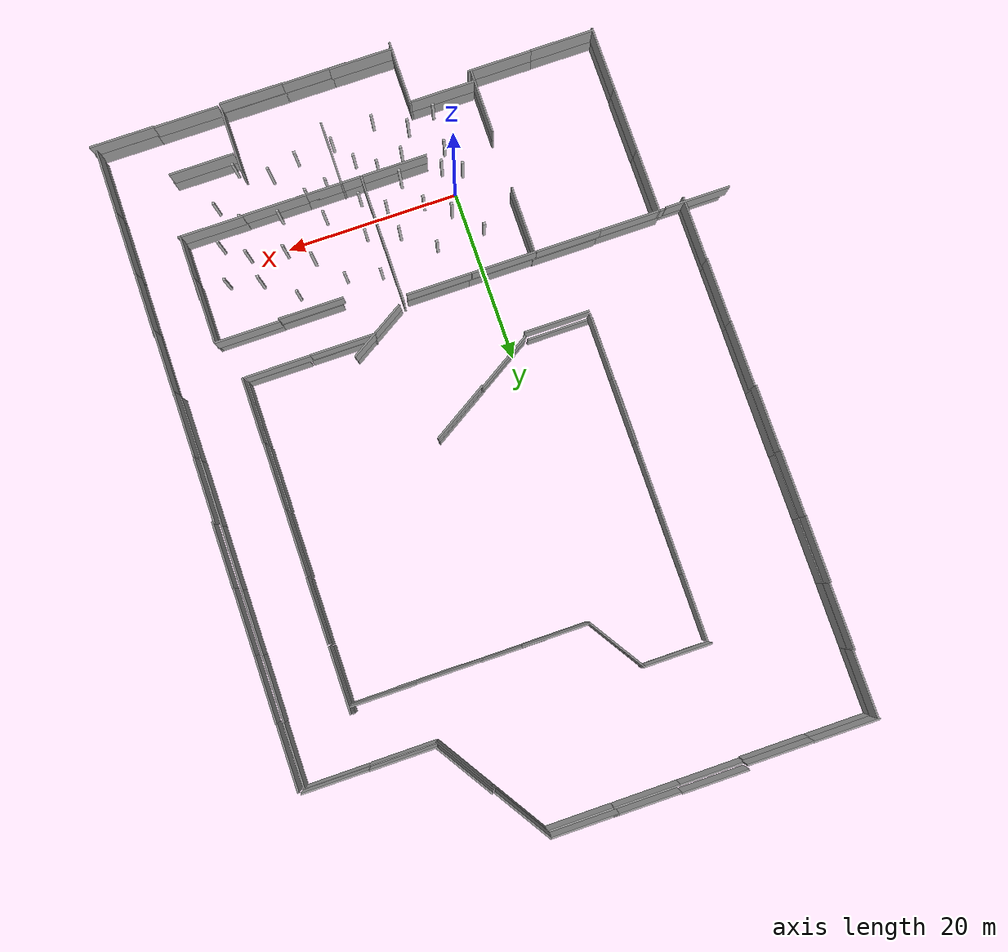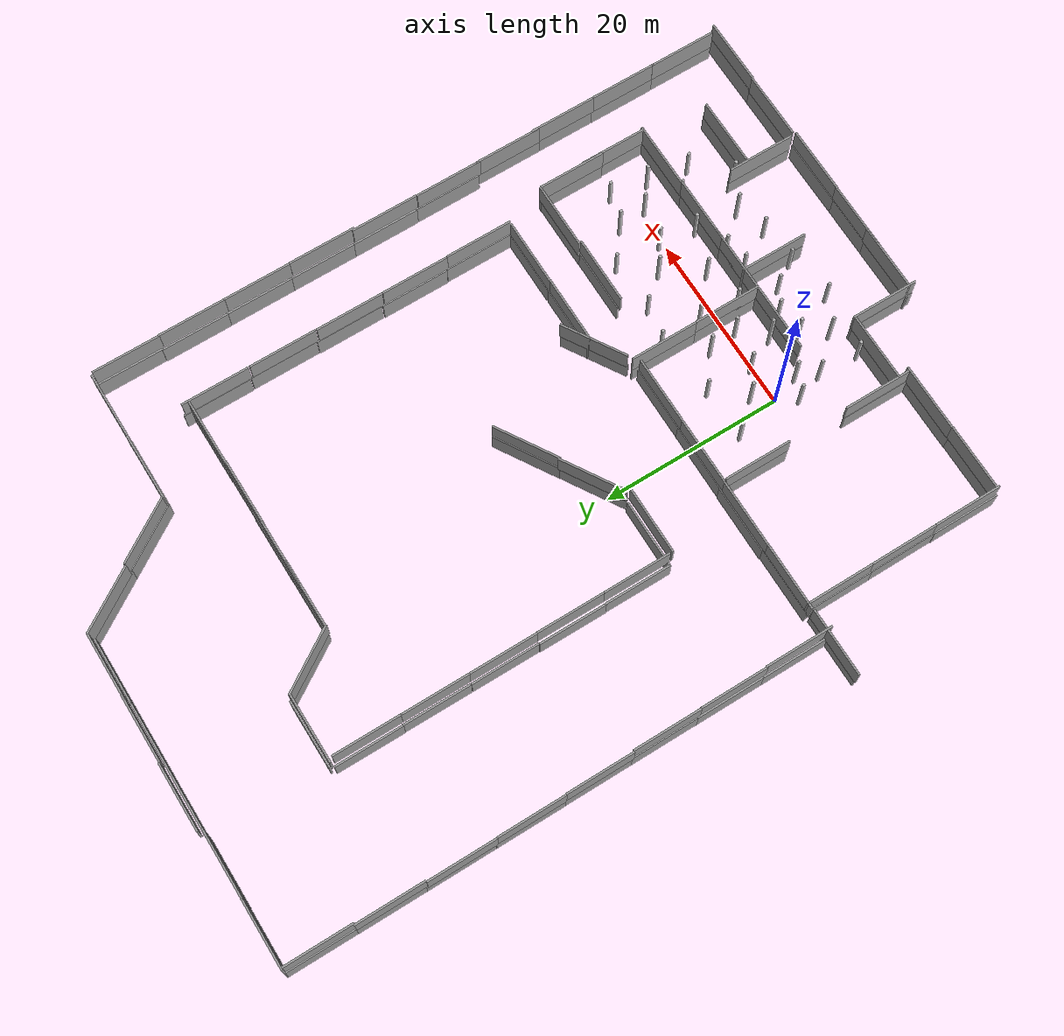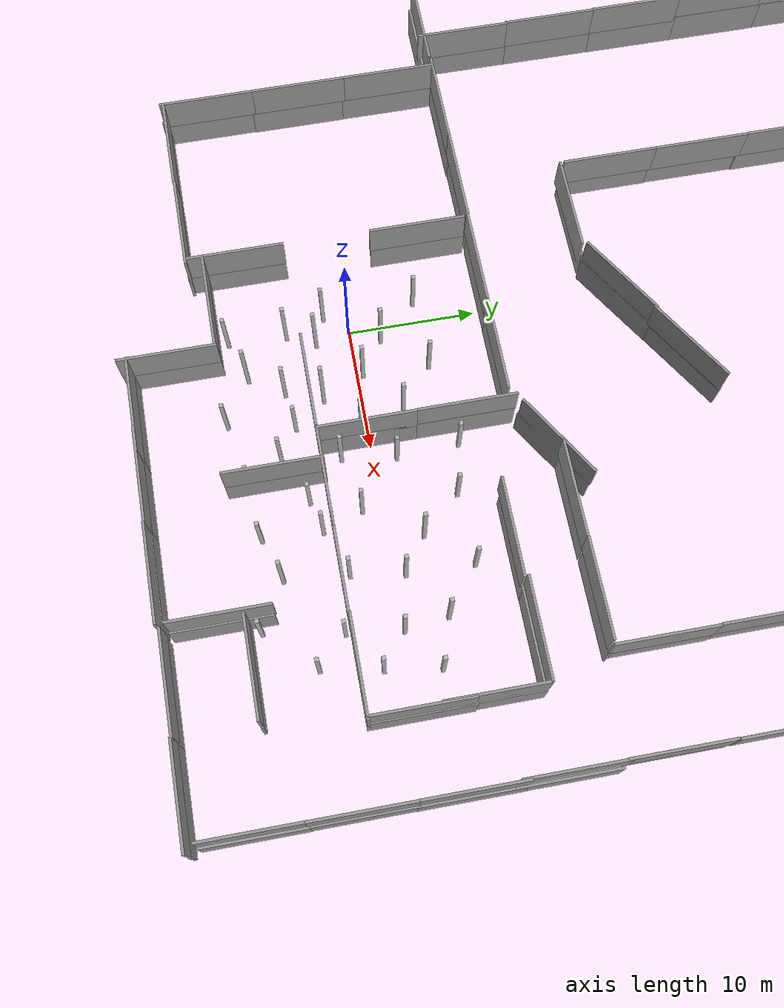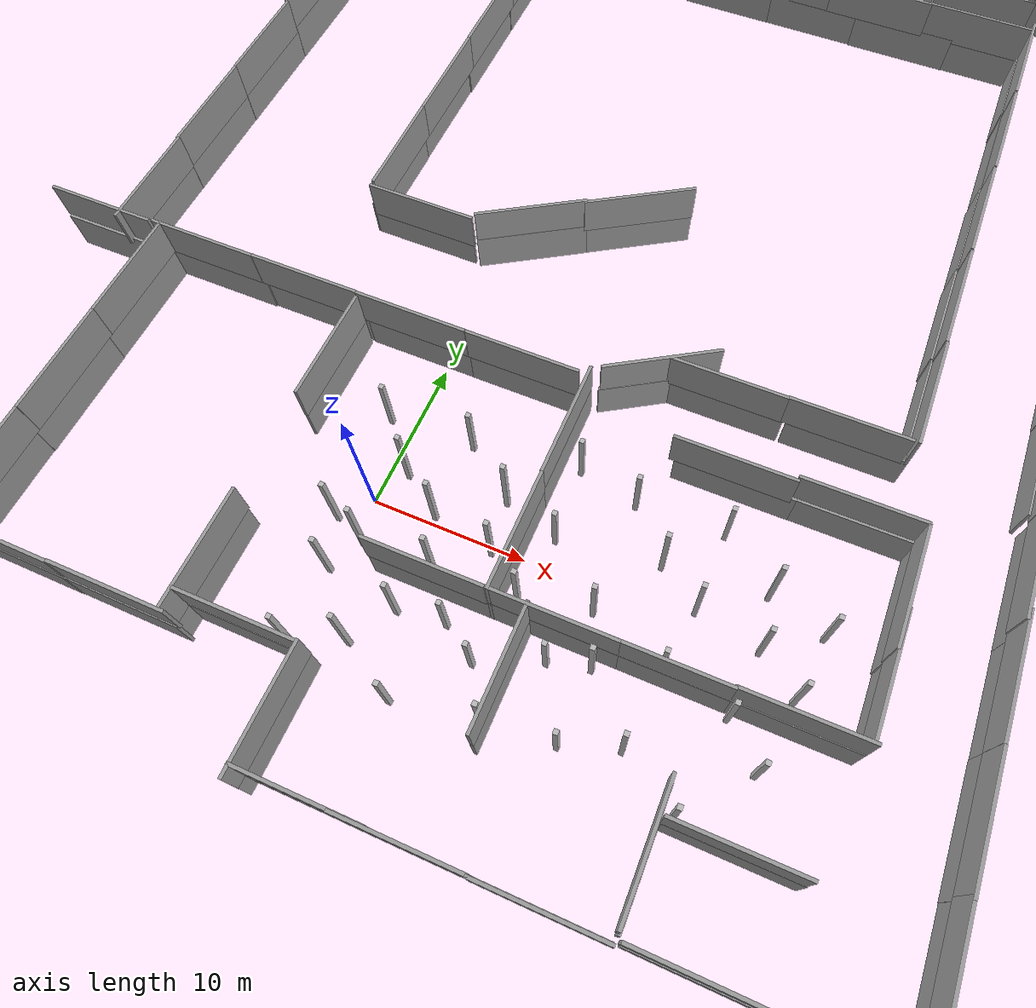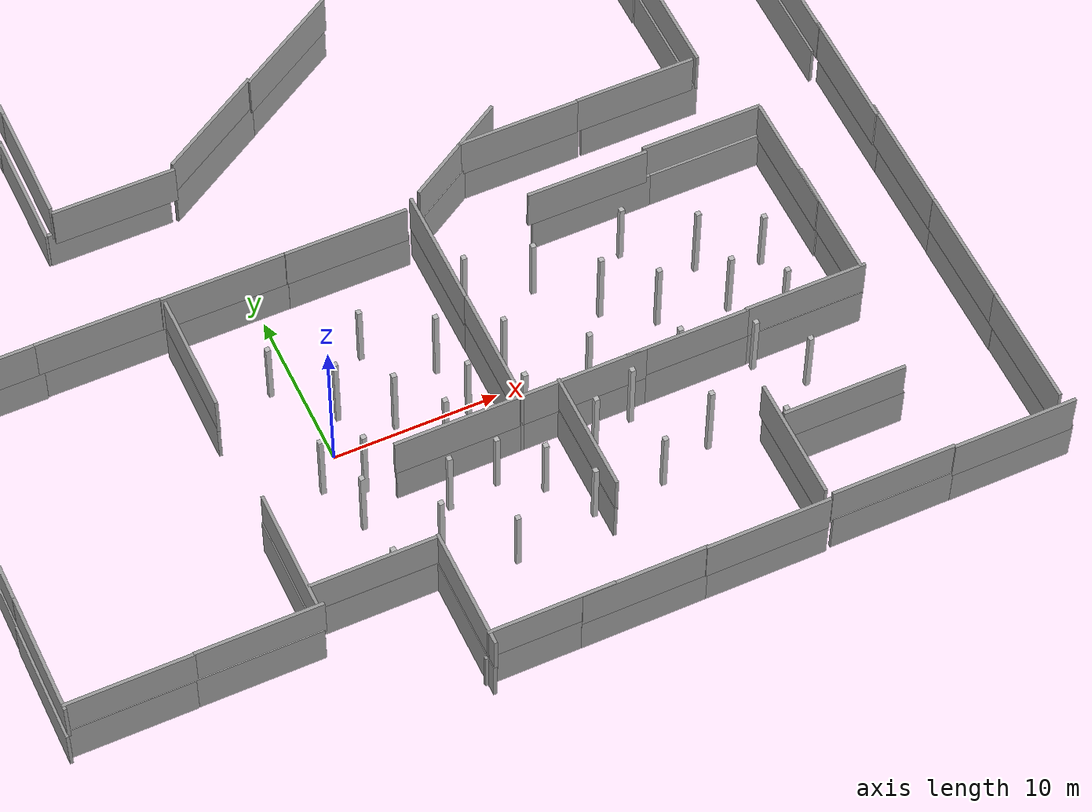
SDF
<sdf version="1.6">
 <world name="world">
  <model name="ground_plane">
   <static>1</static>
   <link name="link">
    <collision name="collision">
     <geometry><plane><normal>0 0 1</normal><size>100 100</size></plane></geometry>
     <surface><friction><ode><mu>100</mu><mu2>50</mu2></ode></friction></surface>
    </collision>
    <velocity_decay><linear>0</linear><angular>0</angular></velocity_decay>
   </link>
  </model>
  <model name="pillars">
   <pose>-3.82158 -2.82314 0 0 -0 0</pose>
   <static>1</static>
   <link name="body">
    <visual name="visual">
     <pose>0 0 -0.001 0 -0 0</pose>
     <geometry><mesh><uri>model://pillars/pillars4.dae</uri><scale>1 1 1</scale></mesh></geometry>
    </visual>
    <collision name="pillars">
     <pose>0 0 -0.001 0 -0 0</pose>
     <geometry><mesh><uri>model://pillars/pillars4.dae</uri><scale>1 1 1</scale></mesh></geometry>
    </collision>
    <velocity_decay><linear>0</linear><angular>0</angular></velocity_decay>
   </link>
  </model>
  <physics name="default_physics" default="0" type="ode">
   <max_step_size>0.001</max_step_size>
   <real_time_factor>1</real_time_factor>
   <real_time_update_rate>1000</real_time_update_rate>
  </physics>
  <scene><ambient>0.4 0.4 0.4 1</ambient><background>0.7 0.7 0.7 1</background><shadows>1</shadows></scene>
  <spherical_coordinates>
   <surface_model>EARTH_WGS84</surface_model>
   <latitude_deg>0</latitude_deg>
   <longitude_deg>0</longitude_deg>
   <elevation>0</elevation>
   <heading_deg>0</heading_deg>
  </spherical_coordinates>
  <gravity>0 0 -9.8</gravity>
  <magnetic_field>6e-06 2.3e-05 -4.2e-05</magnetic_field>
  <atmosphere type="adiabatic"/>
  <model name="grey_wall">
   <static>1</static>
   <link name="link">
    <pose>0 0 1.4 0 -0 0</pose>
    <collision name="collision"><geometry><box><size>7.5 0.2 2.8</size></box></geometry></collision>
    <visual name="visual">
     <cast_shadows>0</cast_shadows>
     <geometry><box><size>7.5 0.2 2.8</size></box></geometry>
     <material>
      <script>
       <uri>model://grey_wall/materials/scripts</uri>
       <uri>model://grey_wall/materials/textures</uri>
       <name>vrc/grey_wall</name>
      </script>
     </material>
    </visual>
   </link>
   <pose>13.5722 -3.83891 0 0 -0 0</pose>
  </model>
  <model name="grey_wall_clone">
   <static>1</static>
   <link name="link">
    <pose>0 0 1.4 0 -0 0</pose>
    <collision name="collision"><geometry><box><size>7.5 0.2 2.8</size></box></geometry></collision>
    <visual name="visual">
     <cast_shadows>0</cast_shadows>
     <geometry><box><size>7.5 0.2 2.8</size></box></geometry>
     <material>
      <script>
       <uri>model://grey_wall/materials/scripts</uri>
       <uri>model://grey_wall/materials/textures</uri>
       <name>vrc/grey_wall</name>
      </script>
     </material>
    </visual>
   </link>
   <pose>13.5722 -3.83891 2.5 0 -0 0</pose>
  </model>
  <model name="grey_wall_clone_clone">
   <static>1</static>
   <link name="link">
    <pose>0 0 1.4 0 -0 0</pose>
    <collision name="collision"><geometry><box><size>7.5 0.2 2.8</size></box></geometry></collision>
    <visual name="visual">
     <cast_shadows>0</cast_shadows>
     <geometry><box><size>7.5 0.2 2.8</size></box></geometry>
     <material>
      <script>
       <uri>model://grey_wall/materials/scripts</uri>
       <uri>model://grey_wall/materials/textures</uri>
       <name>vrc/grey_wall</name>
      </script>
     </material>
    </visual>
   </link>
   <pose>9.726 -0.192574 2.5 0 -0 1.57</pose>
  </model>
  <model name="grey_wall_clone_clone_clone">
   <static>1</static>
   <link name="link">
    <pose>0 0 1.4 0 -0 0</pose>
    <collision name="collision"><geometry><box><size>7.5 0.2 2.8</size></box></geometry></collision>
    <visual name="visual">
     <cast_shadows>0</cast_shadows>
     <geometry><box><size>7.5 0.2 2.8</size></box></geometry>
     <material>
      <script>
       <uri>model://grey_wall/materials/scripts</uri>
       <uri>model://grey_wall/materials/textures</uri>
       <name>vrc/grey_wall</name>
      </script>
     </material>
    </visual>
   </link>
   <pose>9.726 -0.192574 0 0 -0 1.57</pose>
  </model>
  <model name="grey_wall_clone_clone_clone_clone">
   <static>1</static>
   <link name="link">
    <pose>0 0 1.4 0 -0 0</pose>
    <collision name="collision"><geometry><box><size>7.5 0.2 2.8</size></box></geometry></collision>
    <visual name="visual">
     <cast_shadows>0</cast_shadows>
     <geometry><box><size>7.5 0.2 2.8</size></box></geometry>
     <material>
      <script>
       <uri>model://grey_wall/materials/scripts</uri>
       <uri>model://grey_wall/materials/textures</uri>
       <name>vrc/grey_wall</name>
      </script>
     </material>
    </visual>
   </link>
   <pose>9.72423 7.25977 0 0 -0 1.57</pose>
  </model>
  <model name="grey_wall_clone_clone_clone_0">
   <static>1</static>
   <link name="link">
    <pose>0 0 1.4 0 -0 0</pose>
    <collision name="collision"><geometry><box><size>7.5 0.2 2.8</size></box></geometry></collision>
    <visual name="visual">
     <cast_shadows>0</cast_shadows>
     <geometry><box><size>7.5 0.2 2.8</size></box></geometry>
     <material>
      <script>
       <uri>model://grey_wall/materials/scripts</uri>
       <uri>model://grey_wall/materials/textures</uri>
       <name>vrc/grey_wall</name>
      </script>
     </material>
    </visual>
   </link>
   <pose>9.7042 7.30584 2.5 0 -0 1.57</pose>
  </model>
  <model name="grey_wall_clone_0">
   <static>1</static>
   <link name="link">
    <pose>0 0 1.4 0 -0 0</pose>
    <collision name="collision"><geometry><box><size>7.5 0.2 2.8</size></box></geometry></collision>
    <visual name="visual">
     <cast_shadows>0</cast_shadows>
     <geometry><box><size>7.5 0.2 2.8</size></box></geometry>
     <material>
      <script>
       <uri>model://grey_wall/materials/scripts</uri>
       <uri>model://grey_wall/materials/textures</uri>
       <name>vrc/grey_wall</name>
      </script>
     </material>
    </visual>
   </link>
   <pose>5.52403 10.5022 0 0 -0 0</pose>
  </model>
  <model name="grey_wall_clone_clone_0">
   <static>1</static>
   <link name="link">
    <pose>0 0 1.4 0 -0 0</pose>
    <collision name="collision"><geometry><box><size>7.5 0.2 2.8</size></box></geometry></collision>
    <visual name="visual">
     <cast_shadows>0</cast_shadows>
     <geometry><box><size>7.5 0.2 2.8</size></box></geometry>
     <material>
      <script>
       <uri>model://grey_wall/materials/scripts</uri>
       <uri>model://grey_wall/materials/textures</uri>
       <name>vrc/grey_wall</name>
      </script>
     </material>
    </visual>
   </link>
   <pose>5.43048 10.4463 2.5 0 -0 0</pose>
  </model>
  <model name="grey_wall_clone_0_clone">
   <static>1</static>
   <link name="link">
    <pose>0 0 1.4 0 -0 0</pose>
    <collision name="collision"><geometry><box><size>7.5 0.2 2.8</size></box></geometry></collision>
    <visual name="visual">
     <cast_shadows>0</cast_shadows>
     <geometry><box><size>7.5 0.2 2.8</size></box></geometry>
     <material>
      <script>
       <uri>model://grey_wall/materials/scripts</uri>
       <uri>model://grey_wall/materials/textures</uri>
       <name>vrc/grey_wall</name>
      </script>
     </material>
    </visual>
   </link>
   <pose>-1.73699 10.5164 0 0 -0 0</pose>
  </model>
  <model name="grey_wall_clone_clone_0_clone">
   <static>1</static>
   <link name="link">
    <pose>0 0 1.4 0 -0 0</pose>
    <collision name="collision"><geometry><box><size>7.5 0.2 2.8</size></box></geometry></collision>
    <visual name="visual">
     <cast_shadows>0</cast_shadows>
     <geometry><box><size>7.5 0.2 2.8</size></box></geometry>
     <material>
      <script>
       <uri>model://grey_wall/materials/scripts</uri>
       <uri>model://grey_wall/materials/textures</uri>
       <name>vrc/grey_wall</name>
      </script>
     </material>
    </visual>
   </link>
   <pose>-2.10122 10.4554 2.5 0 -0 0</pose>
  </model>
  <model name="grey_wall_clone_clone_clone_clone_clone">
   <static>1</static>
   <link name="link">
    <pose>0 0 1.4 0 -0 0</pose>
    <collision name="collision"><geometry><box><size>7.5 0.2 2.8</size></box></geometry></collision>
    <visual name="visual">
     <cast_shadows>0</cast_shadows>
     <geometry><box><size>7.5 0.2 2.8</size></box></geometry>
     <material>
      <script>
       <uri>model://grey_wall/materials/scripts</uri>
       <uri>model://grey_wall/materials/textures</uri>
       <name>vrc/grey_wall</name>
      </script>
     </material>
    </visual>
   </link>
   <pose>-5.6752 6.4961 0 0 -0 1.57</pose>
  </model>
  <model name="grey_wall_clone_clone_clone_0_clone">
   <static>1</static>
   <link name="link">
    <pose>0 0 1.4 0 -0 0</pose>
    <collision name="collision"><geometry><box><size>7.5 0.2 2.8</size></box></geometry></collision>
    <visual name="visual">
     <cast_shadows>0</cast_shadows>
     <geometry><box><size>7.5 0.2 2.8</size></box></geometry>
     <material>
      <script>
       <uri>model://grey_wall/materials/scripts</uri>
       <uri>model://grey_wall/materials/textures</uri>
       <name>vrc/grey_wall</name>
      </script>
     </material>
    </visual>
   </link>
   <pose>-5.66781 6.45311 2.5 0 -0 1.57</pose>
  </model>
  <model name="grey_wall_clone_0_clone_clone">
   <static>1</static>
   <link name="link">
    <pose>0 0 1.4 0 -0 0</pose>
    <collision name="collision"><geometry><box><size>7.5 0.2 2.8</size></box></geometry></collision>
    <visual name="visual">
     <cast_shadows>0</cast_shadows>
     <geometry><box><size>7.5 0.2 2.8</size></box></geometry>
     <material>
      <script>
       <uri>model://grey_wall/materials/scripts</uri>
       <uri>model://grey_wall/materials/textures</uri>
       <name>vrc/grey_wall</name>
      </script>
     </material>
    </visual>
   </link>
   <pose>5.8738 -3.84512 0 0 -0 0</pose>
  </model>
  <model name="grey_wall_clone_clone_1">
   <static>1</static>
   <link name="link">
    <pose>0 0 1.4 0 -0 0</pose>
    <collision name="collision"><geometry><box><size>7.5 0.2 2.8</size></box></geometry></collision>
    <visual name="visual">
     <cast_shadows>0</cast_shadows>
     <geometry><box><size>7.5 0.2 2.8</size></box></geometry>
     <material>
      <script>
       <uri>model://grey_wall/materials/scripts</uri>
       <uri>model://grey_wall/materials/textures</uri>
       <name>vrc/grey_wall</name>
      </script>
     </material>
    </visual>
   </link>
   <pose>5.81156 -3.84789 2.5 0 -0 0</pose>
  </model>
  <model name="grey_wall_clone_0_clone_clone_clone">
   <static>1</static>
   <link name="link">
    <pose>0 0 1.4 0 -0 0</pose>
    <collision name="collision"><geometry><box><size>7.5 0.2 2.8</size></box></geometry></collision>
    <visual name="visual">
     <cast_shadows>0</cast_shadows>
     <geometry><box><size>7.5 0.2 2.8</size></box></geometry>
     <material>
      <script>
       <uri>model://grey_wall/materials/scripts</uri>
       <uri>model://grey_wall/materials/textures</uri>
       <name>vrc/grey_wall</name>
      </script>
     </material>
    </visual>
   </link>
   <pose>-1.88628 -10.2551 0 0 -0 0</pose>
  </model>
  <model name="grey_wall_clone_clone_1_clone">
   <static>1</static>
   <link name="link">
    <pose>0 0 1.4 0 -0 0</pose>
    <collision name="collision"><geometry><box><size>7.5 0.2 2.8</size></box></geometry></collision>
    <visual name="visual">
     <cast_shadows>0</cast_shadows>
     <geometry><box><size>7.5 0.2 2.8</size></box></geometry>
     <material>
      <script>
       <uri>model://grey_wall/materials/scripts</uri>
       <uri>model://grey_wall/materials/textures</uri>
       <name>vrc/grey_wall</name>
      </script>
     </material>
    </visual>
   </link>
   <pose>-1.99118 -10.2312 2.5 0 -0 0</pose>
  </model>
  <model name="grey_wall_clone_clone_clone_clone_clone_0_clone_0">
   <static>1</static>
   <link name="link">
    <pose>0 0 1.4 0 -0 0</pose>
    <collision name="collision"><geometry><box><size>7.5 0.2 2.8</size></box></geometry></collision>
    <visual name="visual">
     <cast_shadows>0</cast_shadows>
     <geometry><box><size>7.5 0.2 2.8</size></box></geometry>
     <material>
      <script>
       <uri>model://grey_wall/materials/scripts</uri>
       <uri>model://grey_wall/materials/textures</uri>
       <name>vrc/grey_wall</name>
      </script>
     </material>
    </visual>
   </link>
   <pose>12.0107 -7.4078 0 0 -0 1.57</pose>
  </model>
  <model name="grey_wall_clone_clone_clone_0_clone_0_clone_0">
   <static>1</static>
   <link name="link">
    <pose>0 0 1.4 0 -0 0</pose>
    <collision name="collision"><geometry><box><size>7.5 0.2 2.8</size></box></geometry></collision>
    <visual name="visual">
     <cast_shadows>0</cast_shadows>
     <geometry><box><size>7.5 0.2 2.8</size></box></geometry>
     <material>
      <script>
       <uri>model://grey_wall/materials/scripts</uri>
       <uri>model://grey_wall/materials/textures</uri>
       <name>vrc/grey_wall</name>
      </script>
     </material>
    </visual>
   </link>
   <pose>12.0233 -7.4059 2.5 0 -0 1.57</pose>
  </model>
  <light name="user_point_light_0" type="point">
   <pose>7.28336 -5.6677 1 0 -0 0</pose>
   <diffuse>0.5 0.5 0.5 1</diffuse>
   <specular>0.1 0.1 0.1 1</specular>
   <attenuation>
    <range>20</range>
    <constant>0.5</constant>
    <linear>0.01</linear>
    <quadratic>0.001</quadratic>
   </attenuation>
   <cast_shadows>0</cast_shadows>
   <direction>0 0 -1</direction>
  </light>
  <model name="grey_wall_clone_0_clone_clone_clone_0_clone">
   <static>1</static>
   <link name="link">
    <pose>0 0 1.4 0 -0 0</pose>
    <collision name="collision"><geometry><box><size>7.5 0.2 2.8</size></box></geometry></collision>
    <visual name="visual">
     <cast_shadows>0</cast_shadows>
     <geometry><box><size>7.5 0.2 2.8</size></box></geometry>
     <material>
      <script>
       <uri>model://grey_wall/materials/scripts</uri>
       <uri>model://grey_wall/materials/textures</uri>
       <name>vrc/grey_wall</name>
      </script>
     </material>
    </visual>
   </link>
   <pose>10.9652 -16.8254 0 0 -0 0</pose>
  </model>
  <model name="grey_wall_clone_clone_1_clone_clone_clone">
   <static>1</static>
   <link name="link">
    <pose>0 0 1.4 0 -0 0</pose>
    <collision name="collision"><geometry><box><size>7.5 0.2 2.8</size></box></geometry></collision>
    <visual name="visual">
     <cast_shadows>0</cast_shadows>
     <geometry><box><size>7.5 0.2 2.8</size></box></geometry>
     <material>
      <script>
       <uri>model://grey_wall/materials/scripts</uri>
       <uri>model://grey_wall/materials/textures</uri>
       <name>vrc/grey_wall</name>
      </script>
     </material>
    </visual>
   </link>
   <pose>10.9906 -16.8458 2.5 0 -0 0</pose>
  </model>
  <model name="grey_wall_clone_0_clone_clone_clone_0_clone_clone">
   <static>1</static>
   <link name="link">
    <pose>0 0 1.4 0 -0 0</pose>
    <collision name="collision"><geometry><box><size>7.5 0.2 2.8</size></box></geometry></collision>
    <visual name="visual">
     <cast_shadows>0</cast_shadows>
     <geometry><box><size>7.5 0.2 2.8</size></box></geometry>
     <material>
      <script>
       <uri>model://grey_wall/materials/scripts</uri>
       <uri>model://grey_wall/materials/textures</uri>
       <name>vrc/grey_wall</name>
      </script>
     </material>
    </visual>
   </link>
   <pose>18.339 -16.8254 0 0 -0 0</pose>
  </model>
  <model name="grey_wall_clone_clone_1_clone_clone_clone_clone">
   <static>1</static>
   <link name="link">
    <pose>0 0 1.4 0 -0 0</pose>
    <collision name="collision"><geometry><box><size>7.5 0.2 2.8</size></box></geometry></collision>
    <visual name="visual">
     <cast_shadows>0</cast_shadows>
     <geometry><box><size>7.5 0.2 2.8</size></box></geometry>
     <material>
      <script>
       <uri>model://grey_wall/materials/scripts</uri>
       <uri>model://grey_wall/materials/textures</uri>
       <name>vrc/grey_wall</name>
      </script>
     </material>
    </visual>
   </link>
   <pose>18.3322 -16.8956 2.5 0 -0 0</pose>
  </model>
  <model name="grey_wall_clone_clone_clone_clone_clone_0_clone_0_clone_0">
   <static>1</static>
   <link name="link">
    <pose>0 0 1.4 0 -0 0</pose>
    <collision name="collision"><geometry><box><size>7.5 0.2 2.8</size></box></geometry></collision>
    <visual name="visual">
     <cast_shadows>0</cast_shadows>
     <geometry><box><size>7.5 0.2 2.8</size></box></geometry>
     <material>
      <script>
       <uri>model://grey_wall/materials/scripts</uri>
       <uri>model://grey_wall/materials/textures</uri>
       <name>vrc/grey_wall</name>
      </script>
     </material>
    </visual>
   </link>
   <pose>22.181 -12.6644 0 0 -0 1.57</pose>
  </model>
  <model name="grey_wall_clone_clone_clone_0_clone_0_clone_0_clone_0">
   <static>1</static>
   <link name="link">
    <pose>0 0 1.4 0 -0 0</pose>
    <collision name="collision"><geometry><box><size>7.5 0.2 2.8</size></box></geometry></collision>
    <visual name="visual">
     <cast_shadows>0</cast_shadows>
     <geometry><box><size>7.5 0.2 2.8</size></box></geometry>
     <material>
      <script>
       <uri>model://grey_wall/materials/scripts</uri>
       <uri>model://grey_wall/materials/textures</uri>
       <name>vrc/grey_wall</name>
      </script>
     </material>
    </visual>
   </link>
   <pose>22.0458 -12.5728 2.5 0 -0 1.57</pose>
  </model>
  <model name="grey_wall_clone_1">
   <static>1</static>
   <link name="link">
    <pose>0 0 1.4 0 -0 0</pose>
    <collision name="collision"><geometry><box><size>7.5 0.2 2.8</size></box></geometry></collision>
    <visual name="visual">
     <cast_shadows>0</cast_shadows>
     <geometry><box><size>7.5 0.2 2.8</size></box></geometry>
     <material>
      <script>
       <uri>model://grey_wall/materials/scripts</uri>
       <uri>model://grey_wall/materials/textures</uri>
       <name>vrc/grey_wall</name>
      </script>
     </material>
    </visual>
   </link>
   <pose>19.9134 -3.83819 0 0 -0 0</pose>
  </model>
  <model name="grey_wall_clone_clone_2">
   <static>1</static>
   <link name="link">
    <pose>0 0 1.4 0 -0 0</pose>
    <collision name="collision"><geometry><box><size>7.5 0.2 2.8</size></box></geometry></collision>
    <visual name="visual">
     <cast_shadows>0</cast_shadows>
     <geometry><box><size>7.5 0.2 2.8</size></box></geometry>
     <material>
      <script>
       <uri>model://grey_wall/materials/scripts</uri>
       <uri>model://grey_wall/materials/textures</uri>
       <name>vrc/grey_wall</name>
      </script>
     </material>
    </visual>
   </link>
   <pose>19.8779 -3.83236 2.5 0 -0 0</pose>
  </model>
  <model name="grey_wall_clone_1_clone">
   <static>1</static>
   <link name="link">
    <pose>0 0 1.4 0 -0 0</pose>
    <collision name="collision"><geometry><box><size>7.5 0.2 2.8</size></box></geometry></collision>
    <visual name="visual">
     <cast_shadows>0</cast_shadows>
     <geometry><box><size>7.5 0.2 2.8</size></box></geometry>
     <material>
      <script>
       <uri>model://grey_wall/materials/scripts</uri>
       <uri>model://grey_wall/materials/textures</uri>
       <name>vrc/grey_wall</name>
      </script>
     </material>
    </visual>
   </link>
   <pose>26.1057 -10.8871 0 0 -0 0</pose>
  </model>
  <model name="grey_wall_clone_clone_2_clone">
   <static>1</static>
   <link name="link">
    <pose>0 0 1.4 0 -0 0</pose>
    <collision name="collision"><geometry><box><size>7.5 0.2 2.8</size></box></geometry></collision>
    <visual name="visual">
     <cast_shadows>0</cast_shadows>
     <geometry><box><size>7.5 0.2 2.8</size></box></geometry>
     <material>
      <script>
       <uri>model://grey_wall/materials/scripts</uri>
       <uri>model://grey_wall/materials/textures</uri>
       <name>vrc/grey_wall</name>
      </script>
     </material>
    </visual>
   </link>
   <pose>26.0114 -10.8846 2.5 0 -0 0</pose>
  </model>
  <model name="grey_wall_clone_0_clone_clone_clone_0_clone_clone_clone">
   <static>1</static>
   <link name="link">
    <pose>0 0 1.4 0 -0 0</pose>
    <collision name="collision"><geometry><box><size>7.5 0.2 2.8</size></box></geometry></collision>
    <visual name="visual">
     <cast_shadows>0</cast_shadows>
     <geometry><box><size>7.5 0.2 2.8</size></box></geometry>
     <material>
      <script>
       <uri>model://grey_wall/materials/scripts</uri>
       <uri>model://grey_wall/materials/textures</uri>
       <name>vrc/grey_wall</name>
      </script>
     </material>
    </visual>
   </link>
   <pose>26.1699 -16.7148 0 0 -0 0</pose>
  </model>
  <model name="grey_wall_clone_clone_1_clone_clone_clone_clone_clone">
   <static>1</static>
   <link name="link">
    <pose>0 0 1.4 0 -0 0</pose>
    <collision name="collision"><geometry><box><size>7.5 0.2 2.8</size></box></geometry></collision>
    <visual name="visual">
     <cast_shadows>0</cast_shadows>
     <geometry><box><size>7.5 0.2 2.8</size></box></geometry>
     <material>
      <script>
       <uri>model://grey_wall/materials/scripts</uri>
       <uri>model://grey_wall/materials/textures</uri>
       <name>vrc/grey_wall</name>
      </script>
     </material>
    </visual>
   </link>
   <pose>26.0239 -16.6483 2.5 0 -0 0</pose>
  </model>
  <model name="grey_wall_clone_0_clone_clone_clone_0_clone_clone_clone_clone">
   <static>1</static>
   <link name="link">
    <pose>0 0 1.4 0 -0 0</pose>
    <collision name="collision"><geometry><box><size>7.5 0.2 2.8</size></box></geometry></collision>
    <visual name="visual">
     <cast_shadows>0</cast_shadows>
     <geometry><box><size>7.5 0.2 2.8</size></box></geometry>
     <material>
      <script>
       <uri>model://grey_wall/materials/scripts</uri>
       <uri>model://grey_wall/materials/textures</uri>
       <name>vrc/grey_wall</name>
      </script>
     </material>
    </visual>
   </link>
   <pose>33.5484 -16.7279 0 0 -0 0</pose>
  </model>
  <model name="grey_wall_clone_clone_1_clone_clone_clone_clone_clone_clone">
   <static>1</static>
   <link name="link">
    <pose>0 0 1.4 0 -0 0</pose>
    <collision name="collision"><geometry><box><size>7.5 0.2 2.8</size></box></geometry></collision>
    <visual name="visual">
     <cast_shadows>0</cast_shadows>
     <geometry><box><size>7.5 0.2 2.8</size></box></geometry>
     <material>
      <script>
       <uri>model://grey_wall/materials/scripts</uri>
       <uri>model://grey_wall/materials/textures</uri>
       <name>vrc/grey_wall</name>
      </script>
     </material>
    </visual>
   </link>
   <pose>33.4635 -16.7332 2.5 0 -0 0</pose>
  </model>
  <model name="grey_wall_clone_clone_clone_clone_clone_0_clone_0_clone_0_clone">
   <static>1</static>
   <link name="link">
    <pose>0 0 1.4 0 -0 0</pose>
    <collision name="collision"><geometry><box><size>7.5 0.2 2.8</size></box></geometry></collision>
    <visual name="visual">
     <cast_shadows>0</cast_shadows>
     <geometry><box><size>7.5 0.2 2.8</size></box></geometry>
     <material>
      <script>
       <uri>model://grey_wall/materials/scripts</uri>
       <uri>model://grey_wall/materials/textures</uri>
       <name>vrc/grey_wall</name>
      </script>
     </material>
    </visual>
   </link>
   <pose>36.7704 -12.4742 0 0 -0 1.57</pose>
  </model>
  <model name="grey_wall_clone_clone_clone_0_clone_0_clone_0_clone_0_clone">
   <static>1</static>
   <link name="link">
    <pose>0 0 1.4 0 -0 0</pose>
    <collision name="collision"><geometry><box><size>7.5 0.2 2.8</size></box></geometry></collision>
    <visual name="visual">
     <cast_shadows>0</cast_shadows>
     <geometry><box><size>7.5 0.2 2.8</size></box></geometry>
     <material>
      <script>
       <uri>model://grey_wall/materials/scripts</uri>
       <uri>model://grey_wall/materials/textures</uri>
       <name>vrc/grey_wall</name>
      </script>
     </material>
    </visual>
   </link>
   <pose>36.5808 -12.3883 2.5 0 -0 1.57</pose>
  </model>
  <model name="grey_wall_clone_clone_clone_clone_clone_0_clone_0_clone_0_clone_0">
   <static>1</static>
   <link name="link">
    <pose>0 0 1.4 0 -0 0</pose>
    <collision name="collision"><geometry><box><size>7.5 0.2 2.8</size></box></geometry></collision>
    <visual name="visual">
     <cast_shadows>0</cast_shadows>
     <geometry><box><size>7.5 0.2 2.8</size></box></geometry>
     <material>
      <script>
       <uri>model://grey_wall/materials/scripts</uri>
       <uri>model://grey_wall/materials/textures</uri>
       <name>vrc/grey_wall</name>
      </script>
     </material>
    </visual>
   </link>
   <pose>36.7467 -5.01666 0 0 -0 1.57</pose>
  </model>
  <model name="grey_wall_clone_clone_clone_clone_clone_0_clone_0_clone_0_clone_1">
   <static>1</static>
   <link name="link">
    <pose>0 0 1.4 0 -0 0</pose>
    <collision name="collision"><geometry><box><size>7.5 0.2 2.8</size></box></geometry></collision>
    <visual name="visual">
     <cast_shadows>0</cast_shadows>
     <geometry><box><size>7.5 0.2 2.8</size></box></geometry>
     <material>
      <script>
       <uri>model://grey_wall/materials/scripts</uri>
       <uri>model://grey_wall/materials/textures</uri>
       <name>vrc/grey_wall</name>
      </script>
     </material>
    </visual>
   </link>
   <pose>36.7735 2.25472 0 0 -0 1.57</pose>
  </model>
  <model name="grey_wall_clone_clone_clone_clone_clone_0_clone_0_clone_0_clone_2">
   <static>1</static>
   <link name="link">
    <pose>0 0 1.4 0 -0 0</pose>
    <collision name="collision"><geometry><box><size>7.5 0.2 2.8</size></box></geometry></collision>
    <visual name="visual">
     <cast_shadows>0</cast_shadows>
     <geometry><box><size>7.5 0.2 2.8</size></box></geometry>
     <material>
      <script>
       <uri>model://grey_wall/materials/scripts</uri>
       <uri>model://grey_wall/materials/textures</uri>
       <name>vrc/grey_wall</name>
      </script>
     </material>
    </visual>
   </link>
   <pose>36.766 8.89985 0 0 -0 1.57</pose>
  </model>
  <model name="grey_wall_clone_clone_clone_0_clone_0_clone_0_clone_0_clone_clone">
   <static>1</static>
   <link name="link">
    <pose>0 0 1.4 0 -0 0</pose>
    <collision name="collision"><geometry><box><size>7.5 0.2 2.8</size></box></geometry></collision>
    <visual name="visual">
     <cast_shadows>0</cast_shadows>
     <geometry><box><size>7.5 0.2 2.8</size></box></geometry>
     <material>
      <script>
       <uri>model://grey_wall/materials/scripts</uri>
       <uri>model://grey_wall/materials/textures</uri>
       <name>vrc/grey_wall</name>
      </script>
     </material>
    </visual>
   </link>
   <pose>36.5981 -5.12794 2.5 0 -0 1.57</pose>
  </model>
  <model name="grey_wall_clone_clone_clone_0_clone_0_clone_0_clone_0_clone_clone_0">
   <static>1</static>
   <link name="link">
    <pose>0 0 1.4 0 -0 0</pose>
    <collision name="collision"><geometry><box><size>7.5 0.2 2.8</size></box></geometry></collision>
    <visual name="visual">
     <cast_shadows>0</cast_shadows>
     <geometry><box><size>7.5 0.2 2.8</size></box></geometry>
     <material>
      <script>
       <uri>model://grey_wall/materials/scripts</uri>
       <uri>model://grey_wall/materials/textures</uri>
       <name>vrc/grey_wall</name>
      </script>
     </material>
    </visual>
   </link>
   <pose>36.5932 2.35798 2.5 0 -0 1.57</pose>
  </model>
  <model name="grey_wall_clone_clone_clone_0_clone_0_clone_0_clone_0_clone_clone_1">
   <static>1</static>
   <link name="link">
    <pose>0 0 1.4 0 -0 0</pose>
    <collision name="collision"><geometry><box><size>7.5 0.2 2.8</size></box></geometry></collision>
    <visual name="visual">
     <cast_shadows>0</cast_shadows>
     <geometry><box><size>7.5 0.2 2.8</size></box></geometry>
     <material>
      <script>
       <uri>model://grey_wall/materials/scripts</uri>
       <uri>model://grey_wall/materials/textures</uri>
       <name>vrc/grey_wall</name>
      </script>
     </material>
    </visual>
   </link>
   <pose>36.5068 9.13269 2.5 0 -0 1.57</pose>
  </model>
  <model name="grey_wall_clone_1_clone_0">
   <static>1</static>
   <link name="link">
    <pose>0 0 1.4 0 -0 0</pose>
    <collision name="collision"><geometry><box><size>7.5 0.2 2.8</size></box></geometry></collision>
    <visual name="visual">
     <cast_shadows>0</cast_shadows>
     <geometry><box><size>7.5 0.2 2.8</size></box></geometry>
     <material>
      <script>
       <uri>model://grey_wall/materials/scripts</uri>
       <uri>model://grey_wall/materials/textures</uri>
       <name>vrc/grey_wall</name>
      </script>
     </material>
    </visual>
   </link>
   <pose>27.1784 -3.8213 0 0 -0 0</pose>
  </model>
  <model name="grey_wall_clone_clone_2_clone_0">
   <static>1</static>
   <link name="link">
    <pose>0 0 1.4 0 -0 0</pose>
    <collision name="collision"><geometry><box><size>7.5 0.2 2.8</size></box></geometry></collision>
    <visual name="visual">
     <cast_shadows>0</cast_shadows>
     <geometry><box><size>7.5 0.2 2.8</size></box></geometry>
     <material>
      <script>
       <uri>model://grey_wall/materials/scripts</uri>
       <uri>model://grey_wall/materials/textures</uri>
       <name>vrc/grey_wall</name>
      </script>
     </material>
    </visual>
   </link>
   <pose>27.2363 -3.76144 2.5 0 -0 0</pose>
  </model>
  <model name="grey_wall_clone_clone_clone_clone_clone_0_clone_0_clone_0_clone_3">
   <static>1</static>
   <link name="link">
    <pose>0 0 1.4 0 -0 0</pose>
    <collision name="collision"><geometry><box><size>7.5 0.2 2.8</size></box></geometry></collision>
    <visual name="visual">
     <cast_shadows>0</cast_shadows>
     <geometry><box><size>7.5 0.2 2.8</size></box></geometry>
     <material>
      <script>
       <uri>model://grey_wall/materials/scripts</uri>
       <uri>model://grey_wall/materials/textures</uri>
       <name>vrc/grey_wall</name>
      </script>
     </material>
    </visual>
   </link>
   <pose>30.814 0.065366 0 0 -0 1.57</pose>
  </model>
  <model name="grey_wall_clone_clone_clone_clone_clone_0_clone_0_clone_0_clone_4">
   <static>1</static>
   <link name="link">
    <pose>0 0 1.4 0 -0 0</pose>
    <collision name="collision"><geometry><box><size>7.5 0.2 2.8</size></box></geometry></collision>
    <visual name="visual">
     <cast_shadows>0</cast_shadows>
     <geometry><box><size>7.5 0.2 2.8</size></box></geometry>
     <material>
      <script>
       <uri>model://grey_wall/materials/scripts</uri>
       <uri>model://grey_wall/materials/textures</uri>
       <name>vrc/grey_wall</name>
      </script>
     </material>
    </visual>
   </link>
   <pose>30.7277 5.00437 0 0 -0 1.57</pose>
  </model>
  <model name="grey_wall_clone_clone_clone_0_clone_0_clone_0_clone_1">
   <static>1</static>
   <link name="link">
    <pose>0 0 1.4 0 -0 0</pose>
    <collision name="collision"><geometry><box><size>7.5 0.2 2.8</size></box></geometry></collision>
    <visual name="visual">
     <cast_shadows>0</cast_shadows>
     <geometry><box><size>7.5 0.2 2.8</size></box></geometry>
     <material>
      <script>
       <uri>model://grey_wall/materials/scripts</uri>
       <uri>model://grey_wall/materials/textures</uri>
       <name>vrc/grey_wall</name>
      </script>
     </material>
    </visual>
   </link>
   <pose>30.7033 -0.035155 2.5 0 -0 1.57</pose>
  </model>
  <model name="grey_wall_clone_clone_clone_0_clone_0_clone_0_clone_2">
   <static>1</static>
   <link name="link">
    <pose>0 0 1.4 0 -0 0</pose>
    <collision name="collision"><geometry><box><size>7.5 0.2 2.8</size></box></geometry></collision>
    <visual name="visual">
     <cast_shadows>0</cast_shadows>
     <geometry><box><size>7.5 0.2 2.8</size></box></geometry>
     <material>
      <script>
       <uri>model://grey_wall/materials/scripts</uri>
       <uri>model://grey_wall/materials/textures</uri>
       <name>vrc/grey_wall</name>
      </script>
     </material>
    </visual>
   </link>
   <pose>30.6384 4.99865 2.5 0 -0 1.57</pose>
  </model>
  <model name="grey_wall_clone_1_clone_clone_0">
   <static>1</static>
   <link name="link">
    <pose>0 0 1.4 0 -0 0</pose>
    <collision name="collision"><geometry><box><size>7.5 0.2 2.8</size></box></geometry></collision>
    <visual name="visual">
     <cast_shadows>0</cast_shadows>
     <geometry><box><size>7.5 0.2 2.8</size></box></geometry>
     <material>
      <script>
       <uri>model://grey_wall/materials/scripts</uri>
       <uri>model://grey_wall/materials/textures</uri>
       <name>vrc/grey_wall</name>
      </script>
     </material>
    </visual>
   </link>
   <pose>25.3238 13.5362 0 0 -0 0</pose>
  </model>
  <model name="grey_wall_clone_1_clone_clone_1">
   <static>1</static>
   <link name="link">
    <pose>0 0 1.4 0 -0 0</pose>
    <collision name="collision"><geometry><box><size>7.5 0.2 2.8</size></box></geometry></collision>
    <visual name="visual">
     <cast_shadows>0</cast_shadows>
     <geometry><box><size>7.5 0.2 2.8</size></box></geometry>
     <material>
      <script>
       <uri>model://grey_wall/materials/scripts</uri>
       <uri>model://grey_wall/materials/textures</uri>
       <name>vrc/grey_wall</name>
      </script>
     </material>
    </visual>
   </link>
   <pose>17.6484 13.518 0 0 -0 0</pose>
  </model>
  <model name="grey_wall_clone_clone_2_clone_0_clone_0">
   <static>1</static>
   <link name="link">
    <pose>0 0 1.4 0 -0 0</pose>
    <collision name="collision"><geometry><box><size>7.5 0.2 2.8</size></box></geometry></collision>
    <visual name="visual">
     <cast_shadows>0</cast_shadows>
     <geometry><box><size>7.5 0.2 2.8</size></box></geometry>
     <material>
      <script>
       <uri>model://grey_wall/materials/scripts</uri>
       <uri>model://grey_wall/materials/textures</uri>
       <name>vrc/grey_wall</name>
      </script>
     </material>
    </visual>
   </link>
   <pose>24.947 13.4906 2.5 0 -0 0</pose>
  </model>
  <model name="grey_wall_clone_clone_2_clone_0_clone_1">
   <static>1</static>
   <link name="link">
    <pose>0 0 1.4 0 -0 0</pose>
    <collision name="collision"><geometry><box><size>7.5 0.2 2.8</size></box></geometry></collision>
    <visual name="visual">
     <cast_shadows>0</cast_shadows>
     <geometry><box><size>7.5 0.2 2.8</size></box></geometry>
     <material>
      <script>
       <uri>model://grey_wall/materials/scripts</uri>
       <uri>model://grey_wall/materials/textures</uri>
       <name>vrc/grey_wall</name>
      </script>
     </material>
    </visual>
   </link>
   <pose>17.5123 13.4523 2.5 0 -0 0</pose>
  </model>
  <model name="grey_wall_clone_1_clone_clone_2_clone">
   <static>1</static>
   <link name="link">
    <pose>0 0 1.4 0 -0 0</pose>
    <collision name="collision"><geometry><box><size>7.5 0.2 2.8</size></box></geometry></collision>
    <visual name="visual">
     <cast_shadows>0</cast_shadows>
     <geometry><box><size>7.5 0.2 2.8</size></box></geometry>
     <material>
      <script>
       <uri>model://grey_wall/materials/scripts</uri>
       <uri>model://grey_wall/materials/textures</uri>
       <name>vrc/grey_wall</name>
      </script>
     </material>
    </visual>
   </link>
   <pose>13.3998 13.0991 -0 0 -0 0.55</pose>
  </model>
  <model name="grey_wall_clone_1_clone_clone_2_clone_0">
   <static>1</static>
   <link name="link">
    <pose>0 0 1.4 0 -0 0</pose>
    <collision name="collision"><geometry><box><size>7.5 0.2 2.8</size></box></geometry></collision>
    <visual name="visual">
     <cast_shadows>0</cast_shadows>
     <geometry><box><size>7.5 0.2 2.8</size></box></geometry>
     <material>
      <script>
       <uri>model://grey_wall/materials/scripts</uri>
       <uri>model://grey_wall/materials/textures</uri>
       <name>vrc/grey_wall</name>
      </script>
     </material>
    </visual>
   </link>
   <pose>13.4572 13.209 2.5 0 -0 0.55</pose>
  </model>
  <model name="grey_wall_clone_1_clone_0_clone">
   <static>1</static>
   <link name="link">
    <pose>0 0 1.4 0 -0 0</pose>
    <collision name="collision"><geometry><box><size>7.5 0.2 2.8</size></box></geometry></collision>
    <visual name="visual">
     <cast_shadows>0</cast_shadows>
     <geometry><box><size>7.5 0.2 2.8</size></box></geometry>
     <material>
      <script>
       <uri>model://grey_wall/materials/scripts</uri>
       <uri>model://grey_wall/materials/textures</uri>
       <name>vrc/grey_wall</name>
      </script>
     </material>
    </visual>
   </link>
   <pose>26.9868 8.61492 0 0 -0 0</pose>
  </model>
  <model name="grey_wall_clone_1_clone_0_clone_0">
   <static>1</static>
   <link name="link">
    <pose>0 0 1.4 0 -0 0</pose>
    <collision name="collision"><geometry><box><size>7.5 0.2 2.8</size></box></geometry></collision>
    <visual name="visual">
     <cast_shadows>0</cast_shadows>
     <geometry><box><size>7.5 0.2 2.8</size></box></geometry>
     <material>
      <script>
       <uri>model://grey_wall/materials/scripts</uri>
       <uri>model://grey_wall/materials/textures</uri>
       <name>vrc/grey_wall</name>
      </script>
     </material>
    </visual>
   </link>
   <pose>19.8813 8.59599 0 0 -0 0</pose>
  </model>
  <model name="grey_wall_clone_clone_2_clone_0_clone_2">
   <static>1</static>
   <link name="link">
    <pose>0 0 1.4 0 -0 0</pose>
    <collision name="collision"><geometry><box><size>7.5 0.2 2.8</size></box></geometry></collision>
    <visual name="visual">
     <cast_shadows>0</cast_shadows>
     <geometry><box><size>7.5 0.2 2.8</size></box></geometry>
     <material>
      <script>
       <uri>model://grey_wall/materials/scripts</uri>
       <uri>model://grey_wall/materials/textures</uri>
       <name>vrc/grey_wall</name>
      </script>
     </material>
    </visual>
   </link>
   <pose>26.9348 8.78503 2.5 0 -0 0</pose>
  </model>
  <model name="grey_wall_clone_clone_2_clone_0_clone_3">
   <static>1</static>
   <link name="link">
    <pose>0 0 1.4 0 -0 0</pose>
    <collision name="collision"><geometry><box><size>7.5 0.2 2.8</size></box></geometry></collision>
    <visual name="visual">
     <cast_shadows>0</cast_shadows>
     <geometry><box><size>7.5 0.2 2.8</size></box></geometry>
     <material>
      <script>
       <uri>model://grey_wall/materials/scripts</uri>
       <uri>model://grey_wall/materials/textures</uri>
       <name>vrc/grey_wall</name>
      </script>
     </material>
    </visual>
   </link>
   <pose>19.5591 8.50168 2.5 0 -0 0</pose>
  </model>
  <light name="user_point_light_0_clone" type="point">
   <pose>22.1998 -4.89933 8 0 -0 0</pose>
   <diffuse>0.498039 0.498039 0.498039 1</diffuse>
   <specular>0.0980392 0.0980392 0.0980392 1</specular>
   <direction>0 0 -1</direction>
   <attenuation>
    <range>20</range>
    <constant>0.5</constant>
    <linear>0.01</linear>
    <quadratic>0.001</quadratic>
   </attenuation>
  </light>
  <light name="user_point_light_0_clone_0" type="point">
   <pose>26.1259 -10.288 8 0 -0 0</pose>
   <diffuse>0.498039 0.498039 0.498039 1</diffuse>
   <specular>0.0980392 0.0980392 0.0980392 1</specular>
   <direction>0 0 -1</direction>
   <attenuation>
    <range>20</range>
    <constant>0.5</constant>
    <linear>0.01</linear>
    <quadratic>0.001</quadratic>
   </attenuation>
  </light>
  <audio><device>default</device></audio>
  <model name="grey_wall_clone_clone_0_clone_clone_clone">
   <static>1</static>
   <link name="link">
    <pose>0 0 1.4 0 -0 0</pose>
    <collision name="collision"><geometry><box><size>7.5 0.2 2.8</size></box></geometry></collision>
    <visual name="visual">
     <cast_shadows>0</cast_shadows>
     <geometry><box><size>7.5 0.2 2.8</size></box></geometry>
     <material>
      <script>
       <uri>model://grey_wall/materials/scripts</uri>
       <uri>model://grey_wall/materials/textures</uri>
       <name>vrc/grey_wall</name>
      </script>
     </material>
    </visual>
   </link>
   <pose>-9.61987 10.4873 2.5 0 -0 0</pose>
  </model>
  <model name="grey_wall_clone_0_clone_clone_0">
   <static>1</static>
   <link name="link">
    <pose>0 0 1.4 0 -0 0</pose>
    <collision name="collision"><geometry><box><size>7.5 0.2 2.8</size></box></geometry></collision>
    <visual name="visual">
     <cast_shadows>0</cast_shadows>
     <geometry><box><size>7.5 0.2 2.8</size></box></geometry>
     <material>
      <script>
       <uri>model://grey_wall/materials/scripts</uri>
       <uri>model://grey_wall/materials/textures</uri>
       <name>vrc/grey_wall</name>
      </script>
     </material>
    </visual>
   </link>
   <pose>-9.23745 10.5709 0 0 -0 0</pose>
  </model>
  <model name="grey_wall_clone_0_clone_clone_0_clone">
   <static>1</static>
   <link name="link">
    <pose>0 0 1.4 0 -0 0</pose>
    <collision name="collision"><geometry><box><size>7.5 0.2 2.8</size></box></geometry></collision>
    <visual name="visual">
     <cast_shadows>0</cast_shadows>
     <geometry><box><size>7.5 0.2 2.8</size></box></geometry>
     <material>
      <script>
       <uri>model://grey_wall/materials/scripts</uri>
       <uri>model://grey_wall/materials/textures</uri>
       <name>vrc/grey_wall</name>
      </script>
     </material>
    </visual>
   </link>
   <pose>-16.7445 10.4949 0 0 -0 0</pose>
  </model>
  <model name="grey_wall_clone_clone_0_clone_clone_clone_clone">
   <static>1</static>
   <link name="link">
    <pose>0 0 1.4 0 -0 0</pose>
    <collision name="collision"><geometry><box><size>7.5 0.2 2.8</size></box></geometry></collision>
    <visual name="visual">
     <cast_shadows>0</cast_shadows>
     <geometry><box><size>7.5 0.2 2.8</size></box></geometry>
     <material>
      <script>
       <uri>model://grey_wall/materials/scripts</uri>
       <uri>model://grey_wall/materials/textures</uri>
       <name>vrc/grey_wall</name>
      </script>
     </material>
    </visual>
   </link>
   <pose>-17.0835 10.4723 2.5 0 -0 0</pose>
  </model>
  <model name="grey_wall_clone_clone_clone_clone_clone_clone">
   <static>1</static>
   <link name="link">
    <pose>0 0 1.4 0 -0 0</pose>
    <collision name="collision"><geometry><box><size>7.5 0.2 2.8</size></box></geometry></collision>
    <visual name="visual">
     <cast_shadows>0</cast_shadows>
     <geometry><box><size>7.5 0.2 2.8</size></box></geometry>
     <material>
      <script>
       <uri>model://grey_wall/materials/scripts</uri>
       <uri>model://grey_wall/materials/textures</uri>
       <name>vrc/grey_wall</name>
      </script>
     </material>
    </visual>
   </link>
   <pose>-20.332 6.62145 0 0 -0 1.57</pose>
  </model>
  <model name="grey_wall_clone_clone_clone_0_clone_clone">
   <static>1</static>
   <link name="link">
    <pose>0 0 1.4 0 -0 0</pose>
    <collision name="collision"><geometry><box><size>7.5 0.2 2.8</size></box></geometry></collision>
    <visual name="visual">
     <cast_shadows>0</cast_shadows>
     <geometry><box><size>7.5 0.2 2.8</size></box></geometry>
     <material>
      <script>
       <uri>model://grey_wall/materials/scripts</uri>
       <uri>model://grey_wall/materials/textures</uri>
       <name>vrc/grey_wall</name>
      </script>
     </material>
    </visual>
   </link>
   <pose>-20.2199 6.83363 2.5 0 -0 1.57</pose>
  </model>
  <model name="grey_wall_clone_clone_clone_0_clone_clone_0">
   <static>1</static>
   <link name="link">
    <pose>0 0 1.4 0 -0 0</pose>
    <collision name="collision"><geometry><box><size>7.5 0.2 2.8</size></box></geometry></collision>
    <visual name="visual">
     <cast_shadows>0</cast_shadows>
     <geometry><box><size>7.5 0.2 2.8</size></box></geometry>
     <material>
      <script>
       <uri>model://grey_wall/materials/scripts</uri>
       <uri>model://grey_wall/materials/textures</uri>
       <name>vrc/grey_wall</name>
      </script>
     </material>
    </visual>
   </link>
   <pose>-20.2201 -0.618483 2.5 0 -0 1.57</pose>
  </model>
  <model name="grey_wall_clone_clone_clone_0_clone_clone_1">
   <static>1</static>
   <link name="link">
    <pose>0 0 1.4 0 -0 0</pose>
    <collision name="collision"><geometry><box><size>7.5 0.2 2.8</size></box></geometry></collision>
    <visual name="visual">
     <cast_shadows>0</cast_shadows>
     <geometry><box><size>7.5 0.2 2.8</size></box></geometry>
     <material>
      <script>
       <uri>model://grey_wall/materials/scripts</uri>
       <uri>model://grey_wall/materials/textures</uri>
       <name>vrc/grey_wall</name>
      </script>
     </material>
    </visual>
   </link>
   <pose>-20.2205 -8.13033 2.5 0 -0 1.57</pose>
  </model>
  <model name="grey_wall_clone_clone_clone_clone_clone_clone_0">
   <static>1</static>
   <link name="link">
    <pose>0 0 1.4 0 -0 0</pose>
    <collision name="collision"><geometry><box><size>7.5 0.2 2.8</size></box></geometry></collision>
    <visual name="visual">
     <cast_shadows>0</cast_shadows>
     <geometry><box><size>7.5 0.2 2.8</size></box></geometry>
     <material>
      <script>
       <uri>model://grey_wall/materials/scripts</uri>
       <uri>model://grey_wall/materials/textures</uri>
       <name>vrc/grey_wall</name>
      </script>
     </material>
    </visual>
   </link>
   <pose>-20.3209 -0.845609 0 0 -0 1.57</pose>
  </model>
  <model name="grey_wall_clone_clone_clone_clone_clone_clone_1">
   <static>1</static>
   <link name="link">
    <pose>0 0 1.4 0 -0 0</pose>
    <collision name="collision"><geometry><box><size>7.5 0.2 2.8</size></box></geometry></collision>
    <visual name="visual">
     <cast_shadows>0</cast_shadows>
     <geometry><box><size>7.5 0.2 2.8</size></box></geometry>
     <material>
      <script>
       <uri>model://grey_wall/materials/scripts</uri>
       <uri>model://grey_wall/materials/textures</uri>
       <name>vrc/grey_wall</name>
      </script>
     </material>
    </visual>
   </link>
   <pose>-20.3764 -8.29871 0 0 -0 1.57</pose>
  </model>
  <model name="grey_wall_clone_0_clone_clone_0_clone_clone">
   <static>1</static>
   <link name="link">
    <pose>0 0 1.4 0 -0 0</pose>
    <collision name="collision"><geometry><box><size>7.5 0.2 2.8</size></box></geometry></collision>
    <visual name="visual">
     <cast_shadows>0</cast_shadows>
     <geometry><box><size>7.5 0.2 2.8</size></box></geometry>
     <material>
      <script>
       <uri>model://grey_wall/materials/scripts</uri>
       <uri>model://grey_wall/materials/textures</uri>
       <name>vrc/grey_wall</name>
      </script>
     </material>
    </visual>
   </link>
   <pose>-16.6727 -11.6348 0 0 -0 0</pose>
  </model>
  <model name="grey_wall_clone_0_clone_clone_0_clone_clone_0">
   <static>1</static>
   <link name="link">
    <pose>0 0 1.4 0 -0 0</pose>
    <collision name="collision"><geometry><box><size>7.5 0.2 2.8</size></box></geometry></collision>
    <visual name="visual">
     <cast_shadows>0</cast_shadows>
     <geometry><box><size>7.5 0.2 2.8</size></box></geometry>
     <material>
      <script>
       <uri>model://grey_wall/materials/scripts</uri>
       <uri>model://grey_wall/materials/textures</uri>
       <name>vrc/grey_wall</name>
      </script>
     </material>
    </visual>
   </link>
   <pose>-9.24089 -11.6068 0 0 -0 0</pose>
  </model>
  <model name="grey_wall_clone_clone_0_clone_clone_clone_clone_clone">
   <static>1</static>
   <link name="link">
    <pose>0 0 1.4 0 -0 0</pose>
    <collision name="collision"><geometry><box><size>7.5 0.2 2.8</size></box></geometry></collision>
    <visual name="visual">
     <cast_shadows>0</cast_shadows>
     <geometry><box><size>7.5 0.2 2.8</size></box></geometry>
     <material>
      <script>
       <uri>model://grey_wall/materials/scripts</uri>
       <uri>model://grey_wall/materials/textures</uri>
       <name>vrc/grey_wall</name>
      </script>
     </material>
    </visual>
   </link>
   <pose>-16.5504 -11.5737 2.5 0 -0 0</pose>
  </model>
  <model name="grey_wall_clone_clone_0_clone_clone_clone_clone_clone_0">
   <static>1</static>
   <link name="link">
    <pose>0 0 1.4 0 -0 0</pose>
    <collision name="collision"><geometry><box><size>7.5 0.2 2.8</size></box></geometry></collision>
    <visual name="visual">
     <cast_shadows>0</cast_shadows>
     <geometry><box><size>7.5 0.2 2.8</size></box></geometry>
     <material>
      <script>
       <uri>model://grey_wall/materials/scripts</uri>
       <uri>model://grey_wall/materials/textures</uri>
       <name>vrc/grey_wall</name>
      </script>
     </material>
    </visual>
   </link>
   <pose>-9.11574 -11.5319 2.5 0 -0 0</pose>
  </model>
  <model name="grey_wall_clone_clone_clone_clone_clone_0_clone_clone">
   <static>1</static>
   <link name="link">
    <pose>0 0 1.4 0 -0 0</pose>
    <collision name="collision"><geometry><box><size>7.5 0.2 2.8</size></box></geometry></collision>
    <visual name="visual">
     <cast_shadows>0</cast_shadows>
     <geometry><box><size>7.5 0.2 2.8</size></box></geometry>
     <material>
      <script>
       <uri>model://grey_wall/materials/scripts</uri>
       <uri>model://grey_wall/materials/textures</uri>
       <name>vrc/grey_wall</name>
      </script>
     </material>
    </visual>
   </link>
   <pose>-5.82667 -7.74217 0 0 -0 1.57</pose>
  </model>
  <model name="grey_wall_clone_clone_clone_0_clone_0_clone_clone">
   <static>1</static>
   <link name="link">
    <pose>0 0 1.4 0 -0 0</pose>
    <collision name="collision"><geometry><box><size>7.5 0.2 2.8</size></box></geometry></collision>
    <visual name="visual">
     <cast_shadows>0</cast_shadows>
     <geometry><box><size>7.5 0.2 2.8</size></box></geometry>
     <material>
      <script>
       <uri>model://grey_wall/materials/scripts</uri>
       <uri>model://grey_wall/materials/textures</uri>
       <name>vrc/grey_wall</name>
      </script>
     </material>
    </visual>
   </link>
   <pose>-5.75023 -7.70151 2.5 0 -0 1.57</pose>
  </model>
  <model name="grey_wall_clone_clone_clone_clone_clone_0_clone_0_clone_0_clone_2_clone">
   <static>1</static>
   <link name="link">
    <pose>0 0 1.4 0 -0 0</pose>
    <collision name="collision"><geometry><box><size>7.5 0.2 2.8</size></box></geometry></collision>
    <visual name="visual">
     <cast_shadows>0</cast_shadows>
     <geometry><box><size>7.5 0.2 2.8</size></box></geometry>
     <material>
      <script>
       <uri>model://grey_wall/materials/scripts</uri>
       <uri>model://grey_wall/materials/textures</uri>
       <name>vrc/grey_wall</name>
      </script>
     </material>
    </visual>
   </link>
   <pose>36.3415 16.5605 0 0 -0 1.57</pose>
  </model>
  <model name="grey_wall_clone_clone_clone_clone_clone_0_clone_0_clone_0_clone_2_clone_0">
   <static>1</static>
   <link name="link">
    <pose>0 0 1.4 0 -0 0</pose>
    <collision name="collision"><geometry><box><size>7.5 0.2 2.8</size></box></geometry></collision>
    <visual name="visual">
     <cast_shadows>0</cast_shadows>
     <geometry><box><size>7.5 0.2 2.8</size></box></geometry>
     <material>
      <script>
       <uri>model://grey_wall/materials/scripts</uri>
       <uri>model://grey_wall/materials/textures</uri>
       <name>vrc/grey_wall</name>
      </script>
     </material>
    </visual>
   </link>
   <pose>36.3089 24.0074 0 0 -0 1.57</pose>
  </model>
  <model name="grey_wall_clone_clone_clone_clone_clone_0_clone_0_clone_0_clone_2_clone_1">
   <static>1</static>
   <link name="link">
    <pose>0 0 1.4 0 -0 0</pose>
    <collision name="collision"><geometry><box><size>7.5 0.2 2.8</size></box></geometry></collision>
    <visual name="visual">
     <cast_shadows>0</cast_shadows>
     <geometry><box><size>7.5 0.2 2.8</size></box></geometry>
     <material>
      <script>
       <uri>model://grey_wall/materials/scripts</uri>
       <uri>model://grey_wall/materials/textures</uri>
       <name>vrc/grey_wall</name>
      </script>
     </material>
    </visual>
   </link>
   <pose>36.3137 31.4883 0 0 -0 1.57</pose>
  </model>
  <model name="grey_wall_clone_clone_clone_clone_clone_0_clone_0_clone_0_clone_2_clone_2">
   <static>1</static>
   <link name="link">
    <pose>0 0 1.4 0 -0 0</pose>
    <collision name="collision"><geometry><box><size>7.5 0.2 2.8</size></box></geometry></collision>
    <visual name="visual">
     <cast_shadows>0</cast_shadows>
     <geometry><box><size>7.5 0.2 2.8</size></box></geometry>
     <material>
      <script>
       <uri>model://grey_wall/materials/scripts</uri>
       <uri>model://grey_wall/materials/textures</uri>
       <name>vrc/grey_wall</name>
      </script>
     </material>
    </visual>
   </link>
   <pose>36.3157 38.7822 0 0 -0 1.57</pose>
  </model>
  <model name="grey_wall_clone_clone_clone_clone_clone_0_clone_0_clone_0_clone_2_clone_3">
   <static>1</static>
   <link name="link">
    <pose>0 0 1.4 0 -0 0</pose>
    <collision name="collision"><geometry><box><size>7.5 0.2 2.8</size></box></geometry></collision>
    <visual name="visual">
     <cast_shadows>0</cast_shadows>
     <geometry><box><size>7.5 0.2 2.8</size></box></geometry>
     <material>
      <script>
       <uri>model://grey_wall/materials/scripts</uri>
       <uri>model://grey_wall/materials/textures</uri>
       <name>vrc/grey_wall</name>
      </script>
     </material>
    </visual>
   </link>
   <pose>36.2923 46.1939 0 0 -0 1.57</pose>
  </model>
  <model name="grey_wall_clone_clone_clone_clone_clone_0_clone_0_clone_0_clone_2_clone_4">
   <static>1</static>
   <link name="link">
    <pose>0 0 1.4 0 -0 0</pose>
    <collision name="collision"><geometry><box><size>7.5 0.2 2.8</size></box></geometry></collision>
    <visual name="visual">
     <cast_shadows>0</cast_shadows>
     <geometry><box><size>7.5 0.2 2.8</size></box></geometry>
     <material>
      <script>
       <uri>model://grey_wall/materials/scripts</uri>
       <uri>model://grey_wall/materials/textures</uri>
       <name>vrc/grey_wall</name>
      </script>
     </material>
    </visual>
   </link>
   <pose>36.3588 53.5986 0 0 -0 1.57</pose>
  </model>
  <model name="grey_wall_clone_clone_clone_0_clone_0_clone_0_clone_0_clone_clone_1_clone">
   <static>1</static>
   <link name="link">
    <pose>0 0 1.4 0 -0 0</pose>
    <collision name="collision"><geometry><box><size>7.5 0.2 2.8</size></box></geometry></collision>
    <visual name="visual">
     <cast_shadows>0</cast_shadows>
     <geometry><box><size>7.5 0.2 2.8</size></box></geometry>
     <material>
      <script>
       <uri>model://grey_wall/materials/scripts</uri>
       <uri>model://grey_wall/materials/textures</uri>
       <name>vrc/grey_wall</name>
      </script>
     </material>
    </visual>
   </link>
   <pose>36.4797 16.2032 2.5 0 -0 1.57</pose>
  </model>
  <model name="grey_wall_clone_clone_clone_0_clone_0_clone_0_clone_0_clone_clone_1_clone_0">
   <static>1</static>
   <link name="link">
    <pose>0 0 1.4 0 -0 0</pose>
    <collision name="collision"><geometry><box><size>7.5 0.2 2.8</size></box></geometry></collision>
    <visual name="visual">
     <cast_shadows>0</cast_shadows>
     <geometry><box><size>7.5 0.2 2.8</size></box></geometry>
     <material>
      <script>
       <uri>model://grey_wall/materials/scripts</uri>
       <uri>model://grey_wall/materials/textures</uri>
       <name>vrc/grey_wall</name>
      </script>
     </material>
    </visual>
   </link>
   <pose>36.5252 23.7606 2.5 0 -0 1.57</pose>
  </model>
  <model name="grey_wall_clone_clone_clone_0_clone_0_clone_0_clone_0_clone_clone_1_clone_1">
   <static>1</static>
   <link name="link">
    <pose>0 0 1.4 0 -0 0</pose>
    <collision name="collision"><geometry><box><size>7.5 0.2 2.8</size></box></geometry></collision>
    <visual name="visual">
     <cast_shadows>0</cast_shadows>
     <geometry><box><size>7.5 0.2 2.8</size></box></geometry>
     <material>
      <script>
       <uri>model://grey_wall/materials/scripts</uri>
       <uri>model://grey_wall/materials/textures</uri>
       <name>vrc/grey_wall</name>
      </script>
     </material>
    </visual>
   </link>
   <pose>36.7015 30.9843 2.5 0 -0 1.57</pose>
  </model>
  <model name="grey_wall_clone_clone_clone_0_clone_0_clone_0_clone_0_clone_clone_1_clone_2">
   <static>1</static>
   <link name="link">
    <pose>0 0 1.4 0 -0 0</pose>
    <collision name="collision"><geometry><box><size>7.5 0.2 2.8</size></box></geometry></collision>
    <visual name="visual">
     <cast_shadows>0</cast_shadows>
     <geometry><box><size>7.5 0.2 2.8</size></box></geometry>
     <material>
      <script>
       <uri>model://grey_wall/materials/scripts</uri>
       <uri>model://grey_wall/materials/textures</uri>
       <name>vrc/grey_wall</name>
      </script>
     </material>
    </visual>
   </link>
   <pose>36.6707 38.505 2.5 0 -0 1.57</pose>
  </model>
  <model name="grey_wall_clone_clone_clone_0_clone_0_clone_0_clone_0_clone_clone_1_clone_3">
   <static>1</static>
   <link name="link">
    <pose>0 0 1.4 0 -0 0</pose>
    <collision name="collision"><geometry><box><size>7.5 0.2 2.8</size></box></geometry></collision>
    <visual name="visual">
     <cast_shadows>0</cast_shadows>
     <geometry><box><size>7.5 0.2 2.8</size></box></geometry>
     <material>
      <script>
       <uri>model://grey_wall/materials/scripts</uri>
       <uri>model://grey_wall/materials/textures</uri>
       <name>vrc/grey_wall</name>
      </script>
     </material>
    </visual>
   </link>
   <pose>36.6689 45.9649 2.5 0 -0 1.57</pose>
  </model>
  <model name="grey_wall_clone_clone_clone_0_clone_0_clone_0_clone_0_clone_clone_1_clone_4">
   <static>1</static>
   <link name="link">
    <pose>0 0 1.4 0 -0 0</pose>
    <collision name="collision"><geometry><box><size>7.5 0.2 2.8</size></box></geometry></collision>
    <visual name="visual">
     <cast_shadows>0</cast_shadows>
     <geometry><box><size>7.5 0.2 2.8</size></box></geometry>
     <material>
      <script>
       <uri>model://grey_wall/materials/scripts</uri>
       <uri>model://grey_wall/materials/textures</uri>
       <name>vrc/grey_wall</name>
      </script>
     </material>
    </visual>
   </link>
   <pose>36.6242 53.3742 2.5 0 -0 1.57</pose>
  </model>
  <model name="grey_wall_clone_1_clone_clone_0_clone">
   <static>1</static>
   <link name="link">
    <pose>0 0 1.4 0 -0 0</pose>
    <collision name="collision"><geometry><box><size>7.5 0.2 2.8</size></box></geometry></collision>
    <visual name="visual">
     <cast_shadows>0</cast_shadows>
     <geometry><box><size>7.5 0.2 2.8</size></box></geometry>
     <material>
      <script>
       <uri>model://grey_wall/materials/scripts</uri>
       <uri>model://grey_wall/materials/textures</uri>
       <name>vrc/grey_wall</name>
      </script>
     </material>
    </visual>
   </link>
   <pose>32.7658 57.2504 0 0 -0 0</pose>
  </model>
  <model name="grey_wall_clone_1_clone_clone_0_clone_0">
   <static>1</static>
   <link name="link">
    <pose>0 0 1.4 0 -0 0</pose>
    <collision name="collision"><geometry><box><size>7.5 0.2 2.8</size></box></geometry></collision>
    <visual name="visual">
     <cast_shadows>0</cast_shadows>
     <geometry><box><size>7.5 0.2 2.8</size></box></geometry>
     <material>
      <script>
       <uri>model://grey_wall/materials/scripts</uri>
       <uri>model://grey_wall/materials/textures</uri>
       <name>vrc/grey_wall</name>
      </script>
     </material>
    </visual>
   </link>
   <pose>25.3429 57.2172 0 0 -0 0</pose>
  </model>
  <model name="grey_wall_clone_1_clone_clone_2_clone_clone">
   <static>1</static>
   <link name="link">
    <pose>0 0 1.4 0 -0 0</pose>
    <collision name="collision"><geometry><box><size>7.5 0.2 2.8</size></box></geometry></collision>
    <visual name="visual">
     <cast_shadows>0</cast_shadows>
     <geometry><box><size>7.5 0.2 2.8</size></box></geometry>
     <material>
      <script>
       <uri>model://grey_wall/materials/scripts</uri>
       <uri>model://grey_wall/materials/textures</uri>
       <name>vrc/grey_wall</name>
      </script>
     </material>
    </visual>
   </link>
   <pose>19.4966 60.3284 0 0 0 -1</pose>
  </model>
  <model name="grey_wall_clone_1_clone_clone_2_clone_clone_clone">
   <static>1</static>
   <link name="link">
    <pose>0 0 1.4 0 -0 0</pose>
    <collision name="collision"><geometry><box><size>7.5 0.2 2.8</size></box></geometry></collision>
    <visual name="visual">
     <cast_shadows>0</cast_shadows>
     <geometry><box><size>7.5 0.2 2.8</size></box></geometry>
     <material>
      <script>
       <uri>model://grey_wall/materials/scripts</uri>
       <uri>model://grey_wall/materials/textures</uri>
       <name>vrc/grey_wall</name>
      </script>
     </material>
    </visual>
   </link>
   <pose>15.4702 66.5937 0 0 0 -1</pose>
  </model>
  <model name="grey_wall_clone_1_clone_clone_0_clone_1">
   <static>1</static>
   <link name="link">
    <pose>0 0 1.4 0 -0 0</pose>
    <collision name="collision"><geometry><box><size>7.5 0.2 2.8</size></box></geometry></collision>
    <visual name="visual">
     <cast_shadows>0</cast_shadows>
     <geometry><box><size>7.5 0.2 2.8</size></box></geometry>
     <material>
      <script>
       <uri>model://grey_wall/materials/scripts</uri>
       <uri>model://grey_wall/materials/textures</uri>
       <name>vrc/grey_wall</name>
      </script>
     </material>
    </visual>
   </link>
   <pose>9.69868 69.6743 0 0 -0 0</pose>
  </model>
  <model name="grey_wall_clone_1_clone_clone_0_clone_2">
   <static>1</static>
   <link name="link">
    <pose>0 0 1.4 0 -0 0</pose>
    <collision name="collision"><geometry><box><size>7.5 0.2 2.8</size></box></geometry></collision>
    <visual name="visual">
     <cast_shadows>0</cast_shadows>
     <geometry><box><size>7.5 0.2 2.8</size></box></geometry>
     <material>
      <script>
       <uri>model://grey_wall/materials/scripts</uri>
       <uri>model://grey_wall/materials/textures</uri>
       <name>vrc/grey_wall</name>
      </script>
     </material>
    </visual>
   </link>
   <pose>2.16297 69.6795 0 0 -0 0</pose>
  </model>
  <model name="grey_wall_clone_1_clone_clone_0_clone_3">
   <static>1</static>
   <link name="link">
    <pose>0 0 1.4 0 -0 0</pose>
    <collision name="collision"><geometry><box><size>7.5 0.2 2.8</size></box></geometry></collision>
    <visual name="visual">
     <cast_shadows>0</cast_shadows>
     <geometry><box><size>7.5 0.2 2.8</size></box></geometry>
     <material>
      <script>
       <uri>model://grey_wall/materials/scripts</uri>
       <uri>model://grey_wall/materials/textures</uri>
       <name>vrc/grey_wall</name>
      </script>
     </material>
    </visual>
   </link>
   <pose>-5.23101 69.6859 0 0 -0 0</pose>
  </model>
  <model name="grey_wall_clone_1_clone_clone_0_clone_4">
   <static>1</static>
   <link name="link">
    <pose>0 0 1.4 0 -0 0</pose>
    <collision name="collision"><geometry><box><size>7.5 0.2 2.8</size></box></geometry></collision>
    <visual name="visual">
     <cast_shadows>0</cast_shadows>
     <geometry><box><size>7.5 0.2 2.8</size></box></geometry>
     <material>
      <script>
       <uri>model://grey_wall/materials/scripts</uri>
       <uri>model://grey_wall/materials/textures</uri>
       <name>vrc/grey_wall</name>
      </script>
     </material>
    </visual>
   </link>
   <pose>-12.5907 69.5614 0 0 -0 0</pose>
  </model>
  <model name="grey_wall_clone_1_clone_clone_0_clone_5">
   <static>1</static>
   <link name="link">
    <pose>0 0 1.4 0 -0 0</pose>
    <collision name="collision"><geometry><box><size>7.5 0.2 2.8</size></box></geometry></collision>
    <visual name="visual">
     <cast_shadows>0</cast_shadows>
     <geometry><box><size>7.5 0.2 2.8</size></box></geometry>
     <material>
      <script>
       <uri>model://grey_wall/materials/scripts</uri>
       <uri>model://grey_wall/materials/textures</uri>
       <name>vrc/grey_wall</name>
      </script>
     </material>
    </visual>
   </link>
   <pose>-19.7762 69.5922 0 0 -0 0</pose>
  </model>
  <model name="grey_wall_clone_clone_clone_clone_clone_clone_clone">
   <static>1</static>
   <link name="link">
    <pose>0 0 1.4 0 -0 0</pose>
    <collision name="collision"><geometry><box><size>7.5 0.2 2.8</size></box></geometry></collision>
    <visual name="visual">
     <cast_shadows>0</cast_shadows>
     <geometry><box><size>7.5 0.2 2.8</size></box></geometry>
     <material>
      <script>
       <uri>model://grey_wall/materials/scripts</uri>
       <uri>model://grey_wall/materials/textures</uri>
       <name>vrc/grey_wall</name>
      </script>
     </material>
    </visual>
   </link>
   <pose>-23.4447 65.8213 0 0 -0 1.57</pose>
  </model>
  <model name="grey_wall_clone_clone_clone_clone_clone_clone_clone_0">
   <static>1</static>
   <link name="link">
    <pose>0 0 1.4 0 -0 0</pose>
    <collision name="collision"><geometry><box><size>7.5 0.2 2.8</size></box></geometry></collision>
    <visual name="visual">
     <cast_shadows>0</cast_shadows>
     <geometry><box><size>7.5 0.2 2.8</size></box></geometry>
     <material>
      <script>
       <uri>model://grey_wall/materials/scripts</uri>
       <uri>model://grey_wall/materials/textures</uri>
       <name>vrc/grey_wall</name>
      </script>
     </material>
    </visual>
   </link>
   <pose>-23.4677 58.4189 0 0 -0 1.57</pose>
  </model>
  <model name="grey_wall_clone_clone_clone_clone_clone_clone_clone_0_clone">
   <static>1</static>
   <link name="link">
    <pose>0 0 1.4 0 -0 0</pose>
    <collision name="collision"><geometry><box><size>7.5 0.2 2.8</size></box></geometry></collision>
    <visual name="visual">
     <cast_shadows>0</cast_shadows>
     <geometry><box><size>7.5 0.2 2.8</size></box></geometry>
     <material>
      <script>
       <uri>model://grey_wall/materials/scripts</uri>
       <uri>model://grey_wall/materials/textures</uri>
       <name>vrc/grey_wall</name>
      </script>
     </material>
    </visual>
   </link>
   <pose>-23.4789 51.0306 0 0 -0 1.57</pose>
  </model>
  <model name="grey_wall_clone_clone_clone_clone_clone_clone_clone_0_clone_0">
   <static>1</static>
   <link name="link">
    <pose>0 0 1.4 0 -0 0</pose>
    <collision name="collision"><geometry><box><size>7.5 0.2 2.8</size></box></geometry></collision>
    <visual name="visual">
     <cast_shadows>0</cast_shadows>
     <geometry><box><size>7.5 0.2 2.8</size></box></geometry>
     <material>
      <script>
       <uri>model://grey_wall/materials/scripts</uri>
       <uri>model://grey_wall/materials/textures</uri>
       <name>vrc/grey_wall</name>
      </script>
     </material>
    </visual>
   </link>
   <pose>-23.489 43.5185 0 0 -0 1.57</pose>
  </model>
  <model name="grey_wall_clone_clone_clone_clone_clone_clone_clone_0_clone_1">
   <static>1</static>
   <link name="link">
    <pose>0 0 1.4 0 -0 0</pose>
    <collision name="collision"><geometry><box><size>7.5 0.2 2.8</size></box></geometry></collision>
    <visual name="visual">
     <cast_shadows>0</cast_shadows>
     <geometry><box><size>7.5 0.2 2.8</size></box></geometry>
     <material>
      <script>
       <uri>model://grey_wall/materials/scripts</uri>
       <uri>model://grey_wall/materials/textures</uri>
       <name>vrc/grey_wall</name>
      </script>
     </material>
    </visual>
   </link>
   <pose>-23.473 36.1439 0 0 -0 1.57</pose>
  </model>
  <model name="grey_wall_clone_clone_clone_clone_clone_clone_clone_0_clone_2">
   <static>1</static>
   <link name="link">
    <pose>0 0 1.4 0 -0 0</pose>
    <collision name="collision"><geometry><box><size>7.5 0.2 2.8</size></box></geometry></collision>
    <visual name="visual">
     <cast_shadows>0</cast_shadows>
     <geometry><box><size>7.5 0.2 2.8</size></box></geometry>
     <material>
      <script>
       <uri>model://grey_wall/materials/scripts</uri>
       <uri>model://grey_wall/materials/textures</uri>
       <name>vrc/grey_wall</name>
      </script>
     </material>
    </visual>
   </link>
   <pose>-23.4833 28.6502 0 0 -0 1.57</pose>
  </model>
  <model name="grey_wall_clone_clone_clone_clone_clone_clone_clone_0_clone_3">
   <static>1</static>
   <link name="link">
    <pose>0 0 1.4 0 -0 0</pose>
    <collision name="collision"><geometry><box><size>7.5 0.2 2.8</size></box></geometry></collision>
    <visual name="visual">
     <cast_shadows>0</cast_shadows>
     <geometry><box><size>7.5 0.2 2.8</size></box></geometry>
     <material>
      <script>
       <uri>model://grey_wall/materials/scripts</uri>
       <uri>model://grey_wall/materials/textures</uri>
       <name>vrc/grey_wall</name>
      </script>
     </material>
    </visual>
   </link>
   <pose>-23.5068 21.2609 0 0 -0 1.57</pose>
  </model>
  <model name="grey_wall_clone_clone_clone_clone_clone_clone_clone_0_clone_3_clone">
   <static>1</static>
   <link name="link">
    <pose>0 0 1.4 0 -0 0</pose>
    <collision name="collision"><geometry><box><size>7.5 0.2 2.8</size></box></geometry></collision>
    <visual name="visual">
     <cast_shadows>0</cast_shadows>
     <geometry><box><size>7.5 0.2 2.8</size></box></geometry>
     <material>
      <script>
       <uri>model://grey_wall/materials/scripts</uri>
       <uri>model://grey_wall/materials/textures</uri>
       <name>vrc/grey_wall</name>
      </script>
     </material>
    </visual>
   </link>
   <pose>-23.5242 13.8853 0 0 -0 1.57</pose>
  </model>
  <model name="grey_wall_clone_0_clone_clone_0_clone_0">
   <static>1</static>
   <link name="link">
    <pose>0 0 1.4 0 -0 0</pose>
    <collision name="collision"><geometry><box><size>7.5 0.2 2.8</size></box></geometry></collision>
    <visual name="visual">
     <cast_shadows>0</cast_shadows>
     <geometry><box><size>7.5 0.2 2.8</size></box></geometry>
     <material>
      <script>
       <uri>model://grey_wall/materials/scripts</uri>
       <uri>model://grey_wall/materials/textures</uri>
       <name>vrc/grey_wall</name>
      </script>
     </material>
    </visual>
   </link>
   <pose>-24.5011 10.1445 0 0 -0 0</pose>
  </model>
  <model name="grey_wall_clone_1_clone_clone_0_clone_0_clone_0">
   <static>1</static>
   <link name="link">
    <pose>0 0 1.4 0 -0 0</pose>
    <collision name="collision"><geometry><box><size>7.5 0.2 2.8</size></box></geometry></collision>
    <visual name="visual">
     <cast_shadows>0</cast_shadows>
     <geometry><box><size>7.5 0.2 2.8</size></box></geometry>
     <material>
      <script>
       <uri>model://grey_wall/materials/scripts</uri>
       <uri>model://grey_wall/materials/textures</uri>
       <name>vrc/grey_wall</name>
      </script>
     </material>
    </visual>
   </link>
   <pose>20.0872 50.477 0 0 -0 0</pose>
  </model>
  <model name="grey_wall_clone_1_clone_clone_0_clone_0_clone_1">
   <static>1</static>
   <link name="link">
    <pose>0 0 1.4 0 -0 0</pose>
    <collision name="collision"><geometry><box><size>7.5 0.2 2.8</size></box></geometry></collision>
    <visual name="visual">
     <cast_shadows>0</cast_shadows>
     <geometry><box><size>7.5 0.2 2.8</size></box></geometry>
     <material>
      <script>
       <uri>model://grey_wall/materials/scripts</uri>
       <uri>model://grey_wall/materials/textures</uri>
       <name>vrc/grey_wall</name>
      </script>
     </material>
    </visual>
   </link>
   <pose>12.7282 50.5371 0 0 -0 0</pose>
  </model>
  <model name="grey_wall_clone_1_clone_clone_0_clone_0_clone_1_clone">
   <static>1</static>
   <link name="link">
    <pose>0 0 1.4 0 -0 0</pose>
    <collision name="collision"><geometry><box><size>7.5 0.2 2.8</size></box></geometry></collision>
    <visual name="visual">
     <cast_shadows>0</cast_shadows>
     <geometry><box><size>7.5 0.2 2.8</size></box></geometry>
     <material>
      <script>
       <uri>model://grey_wall/materials/scripts</uri>
       <uri>model://grey_wall/materials/textures</uri>
       <name>vrc/grey_wall</name>
      </script>
     </material>
    </visual>
   </link>
   <pose>5.7587 50.5159 0 0 -0 0</pose>
  </model>
  <model name="grey_wall_clone_1_clone_clone_2_clone_clone_clone_0">
   <static>1</static>
   <link name="link">
    <pose>0 0 1.4 0 -0 0</pose>
    <collision name="collision"><geometry><box><size>7.5 0.2 2.8</size></box></geometry></collision>
    <visual name="visual">
     <cast_shadows>0</cast_shadows>
     <geometry><box><size>7.5 0.2 2.8</size></box></geometry>
     <material>
      <script>
       <uri>model://grey_wall/materials/scripts</uri>
       <uri>model://grey_wall/materials/textures</uri>
       <name>vrc/grey_wall</name>
      </script>
     </material>
    </visual>
   </link>
   <pose>0.058133 53.5932 0 0 0 -1</pose>
  </model>
  <model name="grey_wall_clone_1_clone_clone_0_clone_0_clone_1_clone_clone">
   <static>1</static>
   <link name="link">
    <pose>0 0 1.4 0 -0 0</pose>
    <collision name="collision"><geometry><box><size>7.5 0.2 2.8</size></box></geometry></collision>
    <visual name="visual">
     <cast_shadows>0</cast_shadows>
     <geometry><box><size>7.5 0.2 2.8</size></box></geometry>
     <material>
      <script>
       <uri>model://grey_wall/materials/scripts</uri>
       <uri>model://grey_wall/materials/textures</uri>
       <name>vrc/grey_wall</name>
      </script>
     </material>
    </visual>
   </link>
   <pose>-5.57929 56.7918 0 0 -0 0</pose>
  </model>
  <model name="grey_wall_clone_clone_clone_clone_clone_0_clone_0_clone_0_clone_2_clone_clone_3_clone">
   <static>1</static>
   <link name="link">
    <pose>0 0 1.4 0 -0 0</pose>
    <collision name="collision"><geometry><box><size>7.5 0.2 2.8</size></box></geometry></collision>
    <visual name="visual">
     <cast_shadows>0</cast_shadows>
     <geometry><box><size>7.5 0.2 2.8</size></box></geometry>
     <material>
      <script>
       <uri>model://grey_wall/materials/scripts</uri>
       <uri>model://grey_wall/materials/textures</uri>
       <name>vrc/grey_wall</name>
      </script>
     </material>
    </visual>
   </link>
   <pose>-9.50401 52.6586 0 0 -0 1.57</pose>
  </model>
  <model name="grey_wall_clone_clone_clone_clone_clone_0_clone_0_clone_0_clone_2_clone_clone_3_clone_0">
   <static>1</static>
   <link name="link">
    <pose>0 0 1.4 0 -0 0</pose>
    <collision name="collision"><geometry><box><size>7.5 0.2 2.8</size></box></geometry></collision>
    <visual name="visual">
     <cast_shadows>0</cast_shadows>
     <geometry><box><size>7.5 0.2 2.8</size></box></geometry>
     <material>
      <script>
       <uri>model://grey_wall/materials/scripts</uri>
       <uri>model://grey_wall/materials/textures</uri>
       <name>vrc/grey_wall</name>
      </script>
     </material>
    </visual>
   </link>
   <pose>-9.47898 45.2266 0 0 -0 1.57</pose>
  </model>
  <model name="grey_wall_clone_clone_clone_clone_clone_0_clone_0_clone_0_clone_2_clone_clone_3_clone_1">
   <static>1</static>
   <link name="link">
    <pose>0 0 1.4 0 -0 0</pose>
    <collision name="collision"><geometry><box><size>7.5 0.2 2.8</size></box></geometry></collision>
    <visual name="visual">
     <cast_shadows>0</cast_shadows>
     <geometry><box><size>7.5 0.2 2.8</size></box></geometry>
     <material>
      <script>
       <uri>model://grey_wall/materials/scripts</uri>
       <uri>model://grey_wall/materials/textures</uri>
       <name>vrc/grey_wall</name>
      </script>
     </material>
    </visual>
   </link>
   <pose>-9.4947 37.6767 0 0 -0 1.57</pose>
  </model>
  <model name="grey_wall_clone_clone_clone_clone_clone_0_clone_0_clone_0_clone_2_clone_clone_3_clone_2">
   <static>1</static>
   <link name="link">
    <pose>0 0 1.4 0 -0 0</pose>
    <collision name="collision"><geometry><box><size>7.5 0.2 2.8</size></box></geometry></collision>
    <visual name="visual">
     <cast_shadows>0</cast_shadows>
     <geometry><box><size>7.5 0.2 2.8</size></box></geometry>
     <material>
      <script>
       <uri>model://grey_wall/materials/scripts</uri>
       <uri>model://grey_wall/materials/textures</uri>
       <name>vrc/grey_wall</name>
      </script>
     </material>
    </visual>
   </link>
   <pose>-9.5717 30.1479 0 0 -0 1.57</pose>
  </model>
  <model name="grey_wall_clone_clone_clone_clone_clone_0_clone_0_clone_0_clone_2_clone_clone_3_clone_3">
   <static>1</static>
   <link name="link">
    <pose>0 0 1.4 0 -0 0</pose>
    <collision name="collision"><geometry><box><size>7.5 0.2 2.8</size></box></geometry></collision>
    <visual name="visual">
     <cast_shadows>0</cast_shadows>
     <geometry><box><size>7.5 0.2 2.8</size></box></geometry>
     <material>
      <script>
       <uri>model://grey_wall/materials/scripts</uri>
       <uri>model://grey_wall/materials/textures</uri>
       <name>vrc/grey_wall</name>
      </script>
     </material>
    </visual>
   </link>
   <pose>-9.5391 22.7069 0 0 -0 1.57</pose>
  </model>
  <model name="grey_wall_clone_1_clone_clone_0_clone_0_clone_1_clone_clone_0">
   <static>1</static>
   <link name="link">
    <pose>0 0 1.4 0 -0 0</pose>
    <collision name="collision"><geometry><box><size>7.5 0.2 2.8</size></box></geometry></collision>
    <visual name="visual">
     <cast_shadows>0</cast_shadows>
     <geometry><box><size>7.5 0.2 2.8</size></box></geometry>
     <material>
      <script>
       <uri>model://grey_wall/materials/scripts</uri>
       <uri>model://grey_wall/materials/textures</uri>
       <name>vrc/grey_wall</name>
      </script>
     </material>
    </visual>
   </link>
   <pose>-5.75309 19.0274 0 0 -0 0</pose>
  </model>
  <model name="grey_wall_clone_1_clone_clone_2_clone_clone_0">
   <static>1</static>
   <link name="link">
    <pose>0 0 1.4 0 -0 0</pose>
    <collision name="collision"><geometry><box><size>7.5 0.2 2.8</size></box></geometry></collision>
    <visual name="visual">
     <cast_shadows>0</cast_shadows>
     <geometry><box><size>7.5 0.2 2.8</size></box></geometry>
     <material>
      <script>
       <uri>model://grey_wall/materials/scripts</uri>
       <uri>model://grey_wall/materials/textures</uri>
       <name>vrc/grey_wall</name>
      </script>
     </material>
    </visual>
   </link>
   <pose>1.50407 20.868 -0 0 -0 0.55</pose>
  </model>
  <model name="grey_wall_clone_1_clone_clone_2_clone_clone_1">
   <static>1</static>
   <link name="link">
    <pose>0 0 1.4 0 -0 0</pose>
    <collision name="collision"><geometry><box><size>7.5 0.2 2.8</size></box></geometry></collision>
    <visual name="visual">
     <cast_shadows>0</cast_shadows>
     <geometry><box><size>7.5 0.2 2.8</size></box></geometry>
     <material>
      <script>
       <uri>model://grey_wall/materials/scripts</uri>
       <uri>model://grey_wall/materials/textures</uri>
       <name>vrc/grey_wall</name>
      </script>
     </material>
    </visual>
   </link>
   <pose>7.72291 24.7001 -0 0 -0 0.55</pose>
  </model>
  <model name="grey_wall_clone_clone_clone_clone_clone_0_clone_0_clone_0_clone_2_clone_5">
   <static>1</static>
   <link name="link">
    <pose>0 0 1.4 0 -0 0</pose>
    <collision name="collision"><geometry><box><size>7.5 0.2 2.8</size></box></geometry></collision>
    <visual name="visual">
     <cast_shadows>0</cast_shadows>
     <geometry><box><size>7.5 0.2 2.8</size></box></geometry>
     <material>
      <script>
       <uri>model://grey_wall/materials/scripts</uri>
       <uri>model://grey_wall/materials/textures</uri>
       <name>vrc/grey_wall</name>
      </script>
     </material>
    </visual>
   </link>
   <pose>28.8349 17.386 0 0 -0 1.57</pose>
  </model>
  <model name="grey_wall_clone_clone_clone_clone_clone_0_clone_0_clone_0_clone_2_clone_6">
   <static>1</static>
   <link name="link">
    <pose>0 0 1.4 0 -0 0</pose>
    <collision name="collision"><geometry><box><size>7.5 0.2 2.8</size></box></geometry></collision>
    <visual name="visual">
     <cast_shadows>0</cast_shadows>
     <geometry><box><size>7.5 0.2 2.8</size></box></geometry>
     <material>
      <script>
       <uri>model://grey_wall/materials/scripts</uri>
       <uri>model://grey_wall/materials/textures</uri>
       <name>vrc/grey_wall</name>
      </script>
     </material>
    </visual>
   </link>
   <pose>28.7752 24.9437 0 0 -0 1.57</pose>
  </model>
  <model name="grey_wall_clone_clone_clone_clone_clone_0_clone_0_clone_0_clone_2_clone_7">
   <static>1</static>
   <link name="link">
    <pose>0 0 1.4 0 -0 0</pose>
    <collision name="collision"><geometry><box><size>7.5 0.2 2.8</size></box></geometry></collision>
    <visual name="visual">
     <cast_shadows>0</cast_shadows>
     <geometry><box><size>7.5 0.2 2.8</size></box></geometry>
     <material>
      <script>
       <uri>model://grey_wall/materials/scripts</uri>
       <uri>model://grey_wall/materials/textures</uri>
       <name>vrc/grey_wall</name>
      </script>
     </material>
    </visual>
   </link>
   <pose>28.8403 32.5574 0 0 -0 1.57</pose>
  </model>
  <model name="grey_wall_clone_clone_clone_clone_clone_0_clone_0_clone_0_clone_2_clone_8">
   <static>1</static>
   <link name="link">
    <pose>0 0 1.4 0 -0 0</pose>
    <collision name="collision"><geometry><box><size>7.5 0.2 2.8</size></box></geometry></collision>
    <visual name="visual">
     <cast_shadows>0</cast_shadows>
     <geometry><box><size>7.5 0.2 2.8</size></box></geometry>
     <material>
      <script>
       <uri>model://grey_wall/materials/scripts</uri>
       <uri>model://grey_wall/materials/textures</uri>
       <name>vrc/grey_wall</name>
      </script>
     </material>
    </visual>
   </link>
   <pose>28.921 40.1212 0 0 -0 1.57</pose>
  </model>
  <model name="grey_wall_clone_clone_clone_clone_clone_0_clone_0_clone_0_clone_2_clone_9">
   <static>1</static>
   <link name="link">
    <pose>0 0 1.4 0 -0 0</pose>
    <collision name="collision"><geometry><box><size>7.5 0.2 2.8</size></box></geometry></collision>
    <visual name="visual">
     <cast_shadows>0</cast_shadows>
     <geometry><box><size>7.5 0.2 2.8</size></box></geometry>
     <material>
      <script>
       <uri>model://grey_wall/materials/scripts</uri>
       <uri>model://grey_wall/materials/textures</uri>
       <name>vrc/grey_wall</name>
      </script>
     </material>
    </visual>
   </link>
   <pose>28.8823 47.7359 0 0 -0 1.57</pose>
  </model>
  <model name="grey_wall_clone_1_clone_clone_0_clone_0_clone_0_clone">
   <static>1</static>
   <link name="link">
    <pose>0 0 1.4 0 -0 0</pose>
    <collision name="collision"><geometry><box><size>7.5 0.2 2.8</size></box></geometry></collision>
    <visual name="visual">
     <cast_shadows>0</cast_shadows>
     <geometry><box><size>7.5 0.2 2.8</size></box></geometry>
     <material>
      <script>
       <uri>model://grey_wall/materials/scripts</uri>
       <uri>model://grey_wall/materials/textures</uri>
       <name>vrc/grey_wall</name>
      </script>
     </material>
    </visual>
   </link>
   <pose>24.9695 50.5179 0 0 -0 0</pose>
  </model>
  <model name="grey_wall_clone_clone_clone_0_clone_0_clone_0_clone_0_clone_clone_1_clone_clone">
   <static>1</static>
   <link name="link">
    <pose>0 0 1.4 0 -0 0</pose>
    <collision name="collision"><geometry><box><size>7.5 0.2 2.8</size></box></geometry></collision>
    <visual name="visual">
     <cast_shadows>0</cast_shadows>
     <geometry><box><size>7.5 0.2 2.8</size></box></geometry>
     <material>
      <script>
       <uri>model://grey_wall/materials/scripts</uri>
       <uri>model://grey_wall/materials/textures</uri>
       <name>vrc/grey_wall</name>
      </script>
     </material>
    </visual>
   </link>
   <pose>28.9702 17.1682 2.5 0 -0 1.57</pose>
  </model>
  <model name="grey_wall_clone_clone_clone_0_clone_0_clone_0_clone_0_clone_clone_1_clone_clone_clone">
   <static>1</static>
   <link name="link">
    <pose>0 0 1.4 0 -0 0</pose>
    <collision name="collision"><geometry><box><size>7.5 0.2 2.8</size></box></geometry></collision>
    <visual name="visual">
     <cast_shadows>0</cast_shadows>
     <geometry><box><size>7.5 0.2 2.8</size></box></geometry>
     <material>
      <script>
       <uri>model://grey_wall/materials/scripts</uri>
       <uri>model://grey_wall/materials/textures</uri>
       <name>vrc/grey_wall</name>
      </script>
     </material>
    </visual>
   </link>
   <pose>28.9215 24.6892 2.5 0 -0 1.57</pose>
  </model>
  <model name="grey_wall_clone_clone_clone_0_clone_0_clone_0_clone_0_clone_clone_1_clone_clone_clone_0">
   <static>1</static>
   <link name="link">
    <pose>0 0 1.4 0 -0 0</pose>
    <collision name="collision"><geometry><box><size>7.5 0.2 2.8</size></box></geometry></collision>
    <visual name="visual">
     <cast_shadows>0</cast_shadows>
     <geometry><box><size>7.5 0.2 2.8</size></box></geometry>
     <material>
      <script>
       <uri>model://grey_wall/materials/scripts</uri>
       <uri>model://grey_wall/materials/textures</uri>
       <name>vrc/grey_wall</name>
      </script>
     </material>
    </visual>
   </link>
   <pose>28.9202 32.2853 2.5 0 -0 1.57</pose>
  </model>
  <model name="grey_wall_clone_clone_clone_0_clone_0_clone_0_clone_0_clone_clone_1_clone_clone_clone_1">
   <static>1</static>
   <link name="link">
    <pose>0 0 1.4 0 -0 0</pose>
    <collision name="collision"><geometry><box><size>7.5 0.2 2.8</size></box></geometry></collision>
    <visual name="visual">
     <cast_shadows>0</cast_shadows>
     <geometry><box><size>7.5 0.2 2.8</size></box></geometry>
     <material>
      <script>
       <uri>model://grey_wall/materials/scripts</uri>
       <uri>model://grey_wall/materials/textures</uri>
       <name>vrc/grey_wall</name>
      </script>
     </material>
    </visual>
   </link>
   <pose>28.9586 39.8795 2.5 0 -0 1.57</pose>
  </model>
  <model name="grey_wall_clone_clone_clone_0_clone_0_clone_0_clone_0_clone_clone_1_clone_clone_clone_2">
   <static>1</static>
   <link name="link">
    <pose>0 0 1.4 0 -0 0</pose>
    <collision name="collision"><geometry><box><size>7.5 0.2 2.8</size></box></geometry></collision>
    <visual name="visual">
     <cast_shadows>0</cast_shadows>
     <geometry><box><size>7.5 0.2 2.8</size></box></geometry>
     <material>
      <script>
       <uri>model://grey_wall/materials/scripts</uri>
       <uri>model://grey_wall/materials/textures</uri>
       <name>vrc/grey_wall</name>
      </script>
     </material>
    </visual>
   </link>
   <pose>28.9591 47.5306 2.5 0 -0 1.57</pose>
  </model>
  <model name="grey_wall_clone_clone_2_clone_0_clone_0_clone">
   <static>1</static>
   <link name="link">
    <pose>0 0 1.4 0 -0 0</pose>
    <collision name="collision"><geometry><box><size>7.5 0.2 2.8</size></box></geometry></collision>
    <visual name="visual">
     <cast_shadows>0</cast_shadows>
     <geometry><box><size>7.5 0.2 2.8</size></box></geometry>
     <material>
      <script>
       <uri>model://grey_wall/materials/scripts</uri>
       <uri>model://grey_wall/materials/textures</uri>
       <name>vrc/grey_wall</name>
      </script>
     </material>
    </visual>
   </link>
   <pose>25.1535 50.4983 2.5 0 -0 0</pose>
  </model>
  <model name="grey_wall_clone_clone_2_clone_0_clone_0_clone_0">
   <static>1</static>
   <link name="link">
    <pose>0 0 1.4 0 -0 0</pose>
    <collision name="collision"><geometry><box><size>7.5 0.2 2.8</size></box></geometry></collision>
    <visual name="visual">
     <cast_shadows>0</cast_shadows>
     <geometry><box><size>7.5 0.2 2.8</size></box></geometry>
     <material>
      <script>
       <uri>model://grey_wall/materials/scripts</uri>
       <uri>model://grey_wall/materials/textures</uri>
       <name>vrc/grey_wall</name>
      </script>
     </material>
    </visual>
   </link>
   <pose>17.7308 50.4444 2.5 0 -0 0</pose>
  </model>
  <model name="grey_wall_clone_clone_2_clone_0_clone_0_clone_1">
   <static>1</static>
   <link name="link">
    <pose>0 0 1.4 0 -0 0</pose>
    <collision name="collision"><geometry><box><size>7.5 0.2 2.8</size></box></geometry></collision>
    <visual name="visual">
     <cast_shadows>0</cast_shadows>
     <geometry><box><size>7.5 0.2 2.8</size></box></geometry>
     <material>
      <script>
       <uri>model://grey_wall/materials/scripts</uri>
       <uri>model://grey_wall/materials/textures</uri>
       <name>vrc/grey_wall</name>
      </script>
     </material>
    </visual>
   </link>
   <pose>10.5194 50.4865 2.5 0 -0 0</pose>
  </model>
  <model name="grey_wall_clone_clone_2_clone_0_clone_0_clone_2">
   <static>1</static>
   <link name="link">
    <pose>0 0 1.4 0 -0 0</pose>
    <collision name="collision"><geometry><box><size>7.5 0.2 2.8</size></box></geometry></collision>
    <visual name="visual">
     <cast_shadows>0</cast_shadows>
     <geometry><box><size>7.5 0.2 2.8</size></box></geometry>
     <material>
      <script>
       <uri>model://grey_wall/materials/scripts</uri>
       <uri>model://grey_wall/materials/textures</uri>
       <name>vrc/grey_wall</name>
      </script>
     </material>
    </visual>
   </link>
   <pose>5.86162 50.4517 2.5 0 -0 0</pose>
  </model>
  <model name="grey_wall_clone_1_clone_clone_2_clone_clone_clone_0_clone">
   <static>1</static>
   <link name="link">
    <pose>0 0 1.4 0 -0 0</pose>
    <collision name="collision"><geometry><box><size>7.5 0.2 2.8</size></box></geometry></collision>
    <visual name="visual">
     <cast_shadows>0</cast_shadows>
     <geometry><box><size>7.5 0.2 2.8</size></box></geometry>
     <material>
      <script>
       <uri>model://grey_wall/materials/scripts</uri>
       <uri>model://grey_wall/materials/textures</uri>
       <name>vrc/grey_wall</name>
      </script>
     </material>
    </visual>
   </link>
   <pose>0.058 53.5 2.5 0 0 -1</pose>
  </model>
  <model name="grey_wall_clone_clone_2_clone_0_clone_0_clone_2_clone">
   <static>1</static>
   <link name="link">
    <pose>0 0 1.4 0 -0 0</pose>
    <collision name="collision"><geometry><box><size>7.5 0.2 2.8</size></box></geometry></collision>
    <visual name="visual">
     <cast_shadows>0</cast_shadows>
     <geometry><box><size>7.5 0.2 2.8</size></box></geometry>
     <material>
      <script>
       <uri>model://grey_wall/materials/scripts</uri>
       <uri>model://grey_wall/materials/textures</uri>
       <name>vrc/grey_wall</name>
      </script>
     </material>
    </visual>
   </link>
   <pose>-5.77232 56.5626 2.5 0 -0 0</pose>
  </model>
  <model name="grey_wall_clone_clone_0_clone_clone">
   <static>1</static>
   <link name="link">
    <pose>0 0 1.4 0 -0 0</pose>
    <collision name="collision"><geometry><box><size>7.5 0.2 2.8</size></box></geometry></collision>
    <visual name="visual">
     <cast_shadows>0</cast_shadows>
     <geometry><box><size>7.5 0.2 2.8</size></box></geometry>
     <material>
      <script>
       <uri>model://grey_wall/materials/scripts</uri>
       <uri>model://grey_wall/materials/textures</uri>
       <name>vrc/grey_wall</name>
      </script>
     </material>
    </visual>
   </link>
   <pose>-5.41608 18.5798 2.5 0 -0 0</pose>
  </model>
  <model name="grey_wall_clone_1_clone_clone_2_clone_clone_clone_0_clone_clone_0">
   <static>1</static>
   <link name="link">
    <pose>0 0 1.4 0 -0 0</pose>
    <collision name="collision"><geometry><box><size>7.5 0.2 2.8</size></box></geometry></collision>
    <visual name="visual">
     <cast_shadows>0</cast_shadows>
     <geometry><box><size>7.5 0.2 2.8</size></box></geometry>
     <material>
      <script>
       <uri>model://grey_wall/materials/scripts</uri>
       <uri>model://grey_wall/materials/textures</uri>
       <name>vrc/grey_wall</name>
      </script>
     </material>
    </visual>
   </link>
   <pose>15.2051 66.818 2.5 0 0 -1</pose>
  </model>
  <model name="grey_wall_clone_clone_2_clone_0_clone_0_clone_1_clone_3">
   <static>1</static>
   <link name="link">
    <pose>0 0 1.4 0 -0 0</pose>
    <collision name="collision"><geometry><box><size>7.5 0.2 2.8</size></box></geometry></collision>
    <visual name="visual">
     <cast_shadows>0</cast_shadows>
     <geometry><box><size>7.5 0.2 2.8</size></box></geometry>
     <material>
      <script>
       <uri>model://grey_wall/materials/scripts</uri>
       <uri>model://grey_wall/materials/textures</uri>
       <name>vrc/grey_wall</name>
      </script>
     </material>
    </visual>
   </link>
   <pose>-19.7444 69.5733 2.5 0 -0 0</pose>
  </model>
  <model name="grey_wall_clone_clone_2_clone_0_clone_0_clone_1_clone">
   <static>1</static>
   <link name="link">
    <pose>0 0 1.4 0 -0 0</pose>
    <collision name="collision"><geometry><box><size>7.5 0.2 2.8</size></box></geometry></collision>
    <visual name="visual">
     <cast_shadows>0</cast_shadows>
     <geometry><box><size>7.5 0.2 2.8</size></box></geometry>
     <material>
      <script>
       <uri>model://grey_wall/materials/scripts</uri>
       <uri>model://grey_wall/materials/textures</uri>
       <name>vrc/grey_wall</name>
      </script>
     </material>
    </visual>
   </link>
   <pose>-12.3875 69.5519 2.5 0 -0 0</pose>
  </model>
  <model name="grey_wall_clone_clone_2_clone_0_clone_0_clone_1_clone_0">
   <static>1</static>
   <link name="link">
    <pose>0 0 1.4 0 -0 0</pose>
    <collision name="collision"><geometry><box><size>7.5 0.2 2.8</size></box></geometry></collision>
    <visual name="visual">
     <cast_shadows>0</cast_shadows>
     <geometry><box><size>7.5 0.2 2.8</size></box></geometry>
     <material>
      <script>
       <uri>model://grey_wall/materials/scripts</uri>
       <uri>model://grey_wall/materials/textures</uri>
       <name>vrc/grey_wall</name>
      </script>
     </material>
    </visual>
   </link>
   <pose>-4.92534 70.0392 2.5 0 -0 0</pose>
  </model>
  <model name="grey_wall_clone_clone_2_clone_0_clone_0_clone_1_clone_1">
   <static>1</static>
   <link name="link">
    <pose>0 0 1.4 0 -0 0</pose>
    <collision name="collision"><geometry><box><size>7.5 0.2 2.8</size></box></geometry></collision>
    <visual name="visual">
     <cast_shadows>0</cast_shadows>
     <geometry><box><size>7.5 0.2 2.8</size></box></geometry>
     <material>
      <script>
       <uri>model://grey_wall/materials/scripts</uri>
       <uri>model://grey_wall/materials/textures</uri>
       <name>vrc/grey_wall</name>
      </script>
     </material>
    </visual>
   </link>
   <pose>2.56575 69.9367 2.5 0 -0 0</pose>
  </model>
  <model name="grey_wall_clone_clone_2_clone_0_clone_0_clone_1_clone_2">
   <static>1</static>
   <link name="link">
    <pose>0 0 1.4 0 -0 0</pose>
    <collision name="collision"><geometry><box><size>7.5 0.2 2.8</size></box></geometry></collision>
    <visual name="visual">
     <cast_shadows>0</cast_shadows>
     <geometry><box><size>7.5 0.2 2.8</size></box></geometry>
     <material>
      <script>
       <uri>model://grey_wall/materials/scripts</uri>
       <uri>model://grey_wall/materials/textures</uri>
       <name>vrc/grey_wall</name>
      </script>
     </material>
    </visual>
   </link>
   <pose>9.44687 69.9029 2.5 0 -0 0</pose>
  </model>
  <model name="grey_wall_clone_clone_clone_0_clone_0_clone_0_clone_0_clone_clone_1_clone_4_clone_clone">
   <static>1</static>
   <link name="link">
    <pose>0 0 1.4 0 -0 0</pose>
    <collision name="collision"><geometry><box><size>7.5 0.2 2.8</size></box></geometry></collision>
    <visual name="visual">
     <cast_shadows>0</cast_shadows>
     <geometry><box><size>7.5 0.2 2.8</size></box></geometry>
     <material>
      <script>
       <uri>model://grey_wall/materials/scripts</uri>
       <uri>model://grey_wall/materials/textures</uri>
       <name>vrc/grey_wall</name>
      </script>
     </material>
    </visual>
   </link>
   <pose>-23.3086 65.7391 2.5 0 -0 1.57</pose>
  </model>
  <model name="grey_wall_clone_clone_clone_0_clone_0_clone_0_clone_0_clone_clone_1_clone_4_clone_clone_clone">
   <static>1</static>
   <link name="link">
    <pose>0 0 1.4 0 -0 0</pose>
    <collision name="collision"><geometry><box><size>7.5 0.2 2.8</size></box></geometry></collision>
    <visual name="visual">
     <cast_shadows>0</cast_shadows>
     <geometry><box><size>7.5 0.2 2.8</size></box></geometry>
     <material>
      <script>
       <uri>model://grey_wall/materials/scripts</uri>
       <uri>model://grey_wall/materials/textures</uri>
       <name>vrc/grey_wall</name>
      </script>
     </material>
    </visual>
   </link>
   <pose>-23.4737 58.3955 2.5 0 -0 1.57</pose>
  </model>
  <model name="grey_wall_clone_clone_clone_0_clone_0_clone_0_clone_0_clone_clone_1_clone_4_clone_clone_clone_0">
   <static>1</static>
   <link name="link">
    <pose>0 0 1.4 0 -0 0</pose>
    <collision name="collision"><geometry><box><size>7.5 0.2 2.8</size></box></geometry></collision>
    <visual name="visual">
     <cast_shadows>0</cast_shadows>
     <geometry><box><size>7.5 0.2 2.8</size></box></geometry>
     <material>
      <script>
       <uri>model://grey_wall/materials/scripts</uri>
       <uri>model://grey_wall/materials/textures</uri>
       <name>vrc/grey_wall</name>
      </script>
     </material>
    </visual>
   </link>
   <pose>-23.6053 50.886 2.5 0 -0 1.57</pose>
  </model>
  <model name="grey_wall_clone_clone_clone_0_clone_0_clone_0_clone_0_clone_clone_1_clone_4_clone_clone_clone_1">
   <static>1</static>
   <link name="link">
    <pose>0 0 1.4 0 -0 0</pose>
    <collision name="collision"><geometry><box><size>7.5 0.2 2.8</size></box></geometry></collision>
    <visual name="visual">
     <cast_shadows>0</cast_shadows>
     <geometry><box><size>7.5 0.2 2.8</size></box></geometry>
     <material>
      <script>
       <uri>model://grey_wall/materials/scripts</uri>
       <uri>model://grey_wall/materials/textures</uri>
       <name>vrc/grey_wall</name>
      </script>
     </material>
    </visual>
   </link>
   <pose>-23.5626 43.4287 2.5 0 -0 1.57</pose>
  </model>
  <model name="grey_wall_clone_clone_clone_0_clone_0_clone_0_clone_0_clone_clone_1_clone_4_clone_clone_clone_2">
   <static>1</static>
   <link name="link">
    <pose>0 0 1.4 0 -0 0</pose>
    <collision name="collision"><geometry><box><size>7.5 0.2 2.8</size></box></geometry></collision>
    <visual name="visual">
     <cast_shadows>0</cast_shadows>
     <geometry><box><size>7.5 0.2 2.8</size></box></geometry>
     <material>
      <script>
       <uri>model://grey_wall/materials/scripts</uri>
       <uri>model://grey_wall/materials/textures</uri>
       <name>vrc/grey_wall</name>
      </script>
     </material>
    </visual>
   </link>
   <pose>-23.5033 35.953 2.5 0 -0 1.57</pose>
  </model>
  <model name="grey_wall_clone_clone_clone_0_clone_0_clone_0_clone_0_clone_clone_1_clone_4_clone_clone_clone_3">
   <static>1</static>
   <link name="link">
    <pose>0 0 1.4 0 -0 0</pose>
    <collision name="collision"><geometry><box><size>7.5 0.2 2.8</size></box></geometry></collision>
    <visual name="visual">
     <cast_shadows>0</cast_shadows>
     <geometry><box><size>7.5 0.2 2.8</size></box></geometry>
     <material>
      <script>
       <uri>model://grey_wall/materials/scripts</uri>
       <uri>model://grey_wall/materials/textures</uri>
       <name>vrc/grey_wall</name>
      </script>
     </material>
    </visual>
   </link>
   <pose>-23.3564 28.4543 2.5 0 -0 1.57</pose>
  </model>
  <model name="grey_wall_clone_clone_clone_0_clone_0_clone_0_clone_0_clone_clone_1_clone_4_clone_clone_clone_4">
   <static>1</static>
   <link name="link">
    <pose>0 0 1.4 0 -0 0</pose>
    <collision name="collision"><geometry><box><size>7.5 0.2 2.8</size></box></geometry></collision>
    <visual name="visual">
     <cast_shadows>0</cast_shadows>
     <geometry><box><size>7.5 0.2 2.8</size></box></geometry>
     <material>
      <script>
       <uri>model://grey_wall/materials/scripts</uri>
       <uri>model://grey_wall/materials/textures</uri>
       <name>vrc/grey_wall</name>
      </script>
     </material>
    </visual>
   </link>
   <pose>-23.3169 20.9804 2.5 0 -0 1.57</pose>
  </model>
  <model name="grey_wall_clone_clone_clone_0_clone_0_clone_0_clone_0_clone_clone_1_clone_4_clone_clone_clone_5">
   <static>1</static>
   <link name="link">
    <pose>0 0 1.4 0 -0 0</pose>
    <collision name="collision"><geometry><box><size>7.5 0.2 2.8</size></box></geometry></collision>
    <visual name="visual">
     <cast_shadows>0</cast_shadows>
     <geometry><box><size>7.5 0.2 2.8</size></box></geometry>
     <material>
      <script>
       <uri>model://grey_wall/materials/scripts</uri>
       <uri>model://grey_wall/materials/textures</uri>
       <name>vrc/grey_wall</name>
      </script>
     </material>
    </visual>
   </link>
   <pose>-23.2406 13.6009 2.5 0 -0 1.57</pose>
  </model>
  <model name="grey_wall_clone_clone_0_clone_clone_clone_clone_clone_1">
   <static>1</static>
   <link name="link">
    <pose>0 0 1.4 0 -0 0</pose>
    <collision name="collision"><geometry><box><size>7.5 0.2 2.8</size></box></geometry></collision>
    <visual name="visual">
     <cast_shadows>0</cast_shadows>
     <geometry><box><size>7.5 0.2 2.8</size></box></geometry>
     <material>
      <script>
       <uri>model://grey_wall/materials/scripts</uri>
       <uri>model://grey_wall/materials/textures</uri>
       <name>vrc/grey_wall</name>
      </script>
     </material>
    </visual>
   </link>
   <pose>-24.7558 10.3886 2.5 0 -0 0</pose>
  </model>
  <model name="grey_wall_clone_clone_clone_0_clone_0">
   <static>1</static>
   <link name="link">
    <pose>0 0 1.4 0 -0 0</pose>
    <collision name="collision"><geometry><box><size>7.5 0.2 2.8</size></box></geometry></collision>
    <visual name="visual">
     <cast_shadows>0</cast_shadows>
     <geometry><box><size>7.5 0.2 2.8</size></box></geometry>
     <material>
      <script>
       <uri>model://grey_wall/materials/scripts</uri>
       <uri>model://grey_wall/materials/textures</uri>
       <name>vrc/grey_wall</name>
      </script>
     </material>
    </visual>
   </link>
   <pose>-9.10173 22.6483 2.5 0 -0 1.57</pose>
  </model>
  <model name="grey_wall_clone_clone_clone_0_clone_1">
   <static>1</static>
   <link name="link">
    <pose>0 0 1.4 0 -0 0</pose>
    <collision name="collision"><geometry><box><size>7.5 0.2 2.8</size></box></geometry></collision>
    <visual name="visual">
     <cast_shadows>0</cast_shadows>
     <geometry><box><size>7.5 0.2 2.8</size></box></geometry>
     <material>
      <script>
       <uri>model://grey_wall/materials/scripts</uri>
       <uri>model://grey_wall/materials/textures</uri>
       <name>vrc/grey_wall</name>
      </script>
     </material>
    </visual>
   </link>
   <pose>-9.09434 30.1315 2.5 0 -0 1.57</pose>
  </model>
  <model name="grey_wall_clone_clone_clone_0_clone_2">
   <static>1</static>
   <link name="link">
    <pose>0 0 1.4 0 -0 0</pose>
    <collision name="collision"><geometry><box><size>7.5 0.2 2.8</size></box></geometry></collision>
    <visual name="visual">
     <cast_shadows>0</cast_shadows>
     <geometry><box><size>7.5 0.2 2.8</size></box></geometry>
     <material>
      <script>
       <uri>model://grey_wall/materials/scripts</uri>
       <uri>model://grey_wall/materials/textures</uri>
       <name>vrc/grey_wall</name>
      </script>
     </material>
    </visual>
   </link>
   <pose>-9.1097 37.597 2.5 0 -0 1.57</pose>
  </model>
  <model name="grey_wall_clone_clone_clone_0_clone_3">
   <static>1</static>
   <link name="link">
    <pose>0 0 1.4 0 -0 0</pose>
    <collision name="collision"><geometry><box><size>7.5 0.2 2.8</size></box></geometry></collision>
    <visual name="visual">
     <cast_shadows>0</cast_shadows>
     <geometry><box><size>7.5 0.2 2.8</size></box></geometry>
     <material>
      <script>
       <uri>model://grey_wall/materials/scripts</uri>
       <uri>model://grey_wall/materials/textures</uri>
       <name>vrc/grey_wall</name>
      </script>
     </material>
    </visual>
   </link>
   <pose>-9.10296 45.0316 2.5 0 -0 1.57</pose>
  </model>
  <model name="grey_wall_clone_clone_clone_0_clone_4">
   <static>1</static>
   <link name="link">
    <pose>0 0 1.4 0 -0 0</pose>
    <collision name="collision"><geometry><box><size>7.5 0.2 2.8</size></box></geometry></collision>
    <visual name="visual">
     <cast_shadows>0</cast_shadows>
     <geometry><box><size>7.5 0.2 2.8</size></box></geometry>
     <material>
      <script>
       <uri>model://grey_wall/materials/scripts</uri>
       <uri>model://grey_wall/materials/textures</uri>
       <name>vrc/grey_wall</name>
      </script>
     </material>
    </visual>
   </link>
   <pose>-9.09223 52.435 2.5 0 -0 1.57</pose>
  </model>
  <model name="grey_wall_clone_1_clone_clone_2_clone_clone_clone_0_clone_clone_0_clone">
   <static>1</static>
   <link name="link">
    <pose>0 0 1.4 0 -0 0</pose>
    <collision name="collision"><geometry><box><size>7.5 0.2 2.8</size></box></geometry></collision>
    <visual name="visual">
     <cast_shadows>0</cast_shadows>
     <geometry><box><size>7.5 0.2 2.8</size></box></geometry>
     <material>
      <script>
       <uri>model://grey_wall/materials/scripts</uri>
       <uri>model://grey_wall/materials/textures</uri>
       <name>vrc/grey_wall</name>
      </script>
     </material>
    </visual>
   </link>
   <pose>19.485 60.5637 2.5 0 0 -1</pose>
  </model>
  <model name="grey_wall_clone_clone_2_clone_0_clone_0_clone_clone">
   <static>1</static>
   <link name="link">
    <pose>0 0 1.4 0 -0 0</pose>
    <collision name="collision"><geometry><box><size>7.5 0.2 2.8</size></box></geometry></collision>
    <visual name="visual">
     <cast_shadows>0</cast_shadows>
     <geometry><box><size>7.5 0.2 2.8</size></box></geometry>
     <material>
      <script>
       <uri>model://grey_wall/materials/scripts</uri>
       <uri>model://grey_wall/materials/textures</uri>
       <name>vrc/grey_wall</name>
      </script>
     </material>
    </visual>
   </link>
   <pose>32.6711 57.2957 2.5 0 -0 0</pose>
  </model>
  <model name="grey_wall_clone_clone_2_clone_0_clone_0_clone_clone_0">
   <static>1</static>
   <link name="link">
    <pose>0 0 1.4 0 -0 0</pose>
    <collision name="collision"><geometry><box><size>7.5 0.2 2.8</size></box></geometry></collision>
    <visual name="visual">
     <cast_shadows>0</cast_shadows>
     <geometry><box><size>7.5 0.2 2.8</size></box></geometry>
     <material>
      <script>
       <uri>model://grey_wall/materials/scripts</uri>
       <uri>model://grey_wall/materials/textures</uri>
       <name>vrc/grey_wall</name>
      </script>
     </material>
    </visual>
   </link>
   <pose>25.1533 57.3387 2.5 0 -0 0</pose>
  </model>
  <model name="grey_wall_clone_1_clone_clone_2_clone_0_clone">
   <static>1</static>
   <link name="link">
    <pose>0 0 1.4 0 -0 0</pose>
    <collision name="collision"><geometry><box><size>7.5 0.2 2.8</size></box></geometry></collision>
    <visual name="visual">
     <cast_shadows>0</cast_shadows>
     <geometry><box><size>7.5 0.2 2.8</size></box></geometry>
     <material>
      <script>
       <uri>model://grey_wall/materials/scripts</uri>
       <uri>model://grey_wall/materials/textures</uri>
       <name>vrc/grey_wall</name>
      </script>
     </material>
    </visual>
   </link>
   <pose>1.50187 20.908 2.5 0 -0 0.55</pose>
  </model>
  <model name="grey_wall_clone_1_clone_clone_2_clone_0_clone_0">
   <static>1</static>
   <link name="link">
    <pose>0 0 1.4 0 -0 0</pose>
    <collision name="collision"><geometry><box><size>7.5 0.2 2.8</size></box></geometry></collision>
    <visual name="visual">
     <cast_shadows>0</cast_shadows>
     <geometry><box><size>7.5 0.2 2.8</size></box></geometry>
     <material>
      <script>
       <uri>model://grey_wall/materials/scripts</uri>
       <uri>model://grey_wall/materials/textures</uri>
       <name>vrc/grey_wall</name>
      </script>
     </material>
    </visual>
   </link>
   <pose>7.78394 24.6063 2.5 0 -0 0.55</pose>
  </model>
  <model name="grey_wall_clone_clone_clone_clone_clone_0_clone_0_clone_clone">
   <static>1</static>
   <link name="link">
    <pose>0 0 1.4 0 -0 0</pose>
    <collision name="collision"><geometry><box><size>7.5 0.2 2.8</size></box></geometry></collision>
    <visual name="visual">
     <cast_shadows>0</cast_shadows>
     <geometry><box><size>7.5 0.2 2.8</size></box></geometry>
     <material>
      <script>
       <uri>model://grey_wall/materials/scripts</uri>
       <uri>model://grey_wall/materials/textures</uri>
       <name>vrc/grey_wall</name>
      </script>
     </material>
    </visual>
   </link>
   <pose>1.81162 -13.8472 0 0 -0 1.57</pose>
  </model>
  <model name="grey_wall_clone_clone_clone_0_clone_0_clone_0_clone_clone">
   <static>1</static>
   <link name="link">
    <pose>0 0 1.4 0 -0 0</pose>
    <collision name="collision"><geometry><box><size>7.5 0.2 2.8</size></box></geometry></collision>
    <visual name="visual">
     <cast_shadows>0</cast_shadows>
     <geometry><box><size>7.5 0.2 2.8</size></box></geometry>
     <material>
      <script>
       <uri>model://grey_wall/materials/scripts</uri>
       <uri>model://grey_wall/materials/textures</uri>
       <name>vrc/grey_wall</name>
      </script>
     </material>
    </visual>
   </link>
   <pose>1.85783 -13.8424 2.5 0 -0 1.57</pose>
  </model>
  <model name="grey_wall_clone_0_clone_clone_clone_0_clone_clone_0">
   <static>1</static>
   <link name="link">
    <pose>0 0 1.4 0 -0 0</pose>
    <collision name="collision"><geometry><box><size>7.5 0.2 2.8</size></box></geometry></collision>
    <visual name="visual">
     <cast_shadows>0</cast_shadows>
     <geometry><box><size>7.5 0.2 2.8</size></box></geometry>
     <material>
      <script>
       <uri>model://grey_wall/materials/scripts</uri>
       <uri>model://grey_wall/materials/textures</uri>
       <name>vrc/grey_wall</name>
      </script>
     </material>
    </visual>
   </link>
   <pose>5.28985 -16.8182 0 0 -0 0</pose>
  </model>
  <model name="grey_wall_clone_clone_1_clone_clone_clone_clone_0">
   <static>1</static>
   <link name="link">
    <pose>0 0 1.4 0 -0 0</pose>
    <collision name="collision"><geometry><box><size>7.5 0.2 2.8</size></box></geometry></collision>
    <visual name="visual">
     <cast_shadows>0</cast_shadows>
     <geometry><box><size>7.5 0.2 2.8</size></box></geometry>
     <material>
      <script>
       <uri>model://grey_wall/materials/scripts</uri>
       <uri>model://grey_wall/materials/textures</uri>
       <name>vrc/grey_wall</name>
      </script>
     </material>
    </visual>
   </link>
   <pose>5.47771 -16.8109 2.5 0 -0 0</pose>
  </model>
 </world>
</sdf>
